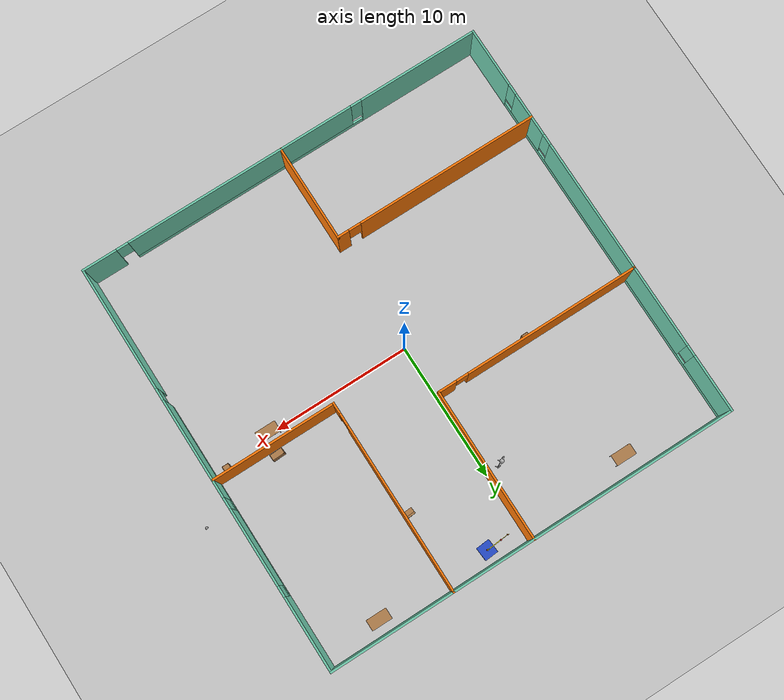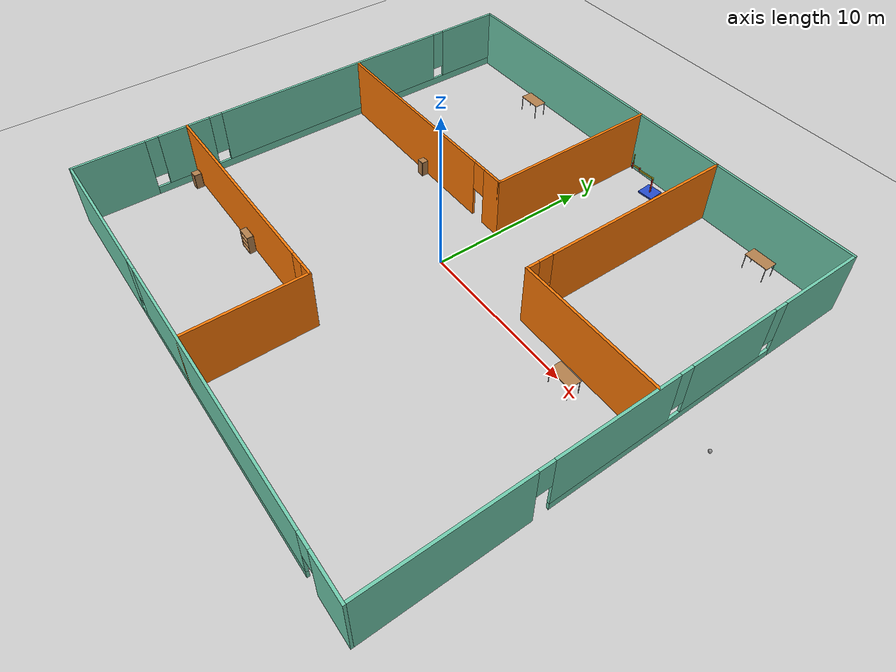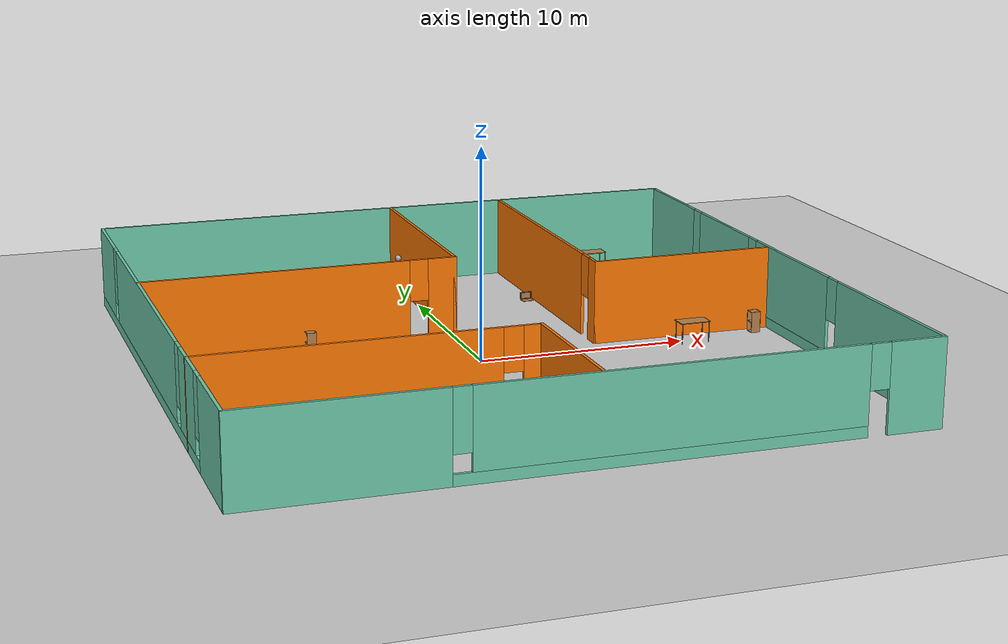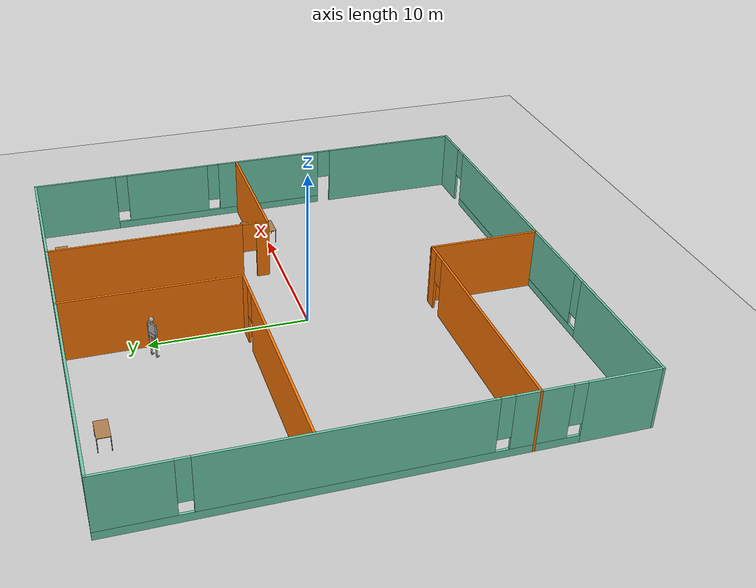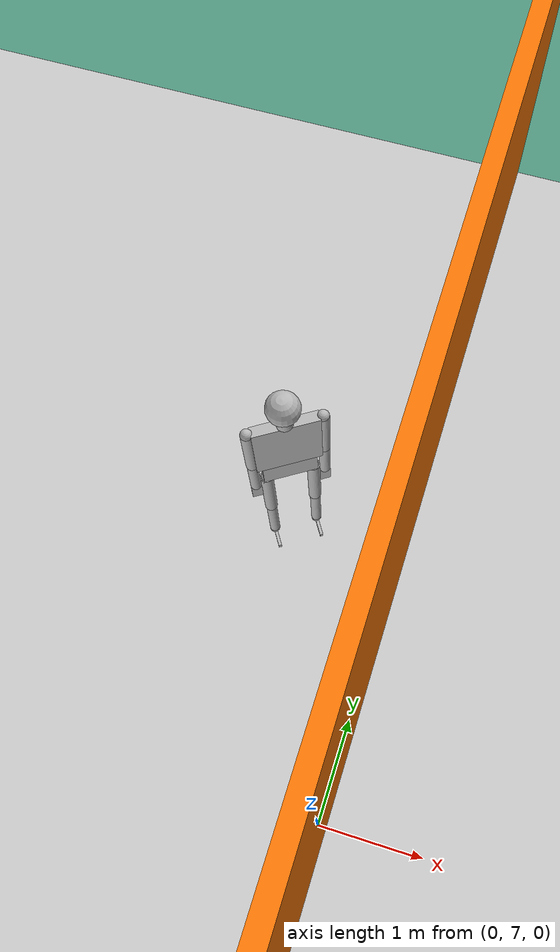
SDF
<sdf version="1.6">
 <world name="default">
  <plugin name="hello" filename="libhello.so"/>
  <light name="sun" type="directional">
   <pose>0 0 10 0 -0 0</pose>
   <diffuse>0.8 0.8 0.8 1</diffuse>
   <specular>0.2 0.2 0.2 1</specular>
   <attenuation>
    <range>1000</range>
    <constant>0.9</constant>
    <linear>0.01</linear>
    <quadratic>0.001</quadratic>
   </attenuation>
   <direction>-0.5 0.1 -0.9</direction>
  </light>
  <model name="ground_plane">
   <static>1</static>
   <link name="link">
    <collision name="collision">
     <geometry><plane><normal>0 0 1</normal><size>100 100</size></plane></geometry>
     <surface>
      <contact><collide_bitmask>65535</collide_bitmask></contact>
      <friction><ode><mu>100</mu><mu2>50</mu2></ode></friction>
     </surface>
    </collision>
    <visual name="visual">
     <cast_shadows>0</cast_shadows>
     <geometry><plane><normal>0 0 1</normal><size>100 100</size></plane></geometry>
     <material>
      <script><uri>file://media/materials/scripts/gazebo.material</uri><name>Gazebo/Grey</name></script>
     </material>
    </visual>
   </link>
  </model>
  <gravity>0 0 -9.8</gravity>
  <magnetic_field>6e-06 2.3e-05 -4.2e-05</magnetic_field>
  <atmosphere type="adiabatic"/>
  <physics name="default_physics" default="0" type="ode">
   <max_step_size>0.001</max_step_size>
   <real_time_factor>1</real_time_factor>
   <real_time_update_rate>1000</real_time_update_rate>
  </physics>
  <scene><ambient>0.4 0.4 0.4 1</ambient><background>0.7 0.7 0.7 1</background><shadows>1</shadows></scene>
  <spherical_coordinates>
   <surface_model>EARTH_WGS84</surface_model>
   <latitude_deg>0</latitude_deg>
   <longitude_deg>0</longitude_deg>
   <elevation>0</elevation>
   <heading_deg>0</heading_deg>
  </spherical_coordinates>
  <model name="mybuilding">
   <link name="Wall_0">
    <pose>0 -15 0 0 -0 0</pose>
    <visual name="Wall_0_Visual_0">
     <pose>-10.633 0 2 0 -0 0</pose>
     <geometry><box><size>8.884 0.15 4</size></box></geometry>
     <material>
      <script><uri>file://media/materials/scripts/gazebo.material</uri><name>Gazebo/Grey</name></script>
      <ambient>0.435294 0.796078 0.67451 1</ambient>
     </material>
     <meta><layer>0</layer></meta>
    </visual>
    <collision name="Wall_0_Collision_0">
     <geometry><box><size>8.884 0.15 4</size></box></geometry>
     <pose>-10.633 0 2 0 -0 0</pose>
    </collision>
    <visual name="Wall_0_Visual_1">
     <pose>13.7885 0 2 0 -0 0</pose>
     <geometry><box><size>2.57292 0.15 4</size></box></geometry>
     <material>
      <script><uri>file://media/materials/scripts/gazebo.material</uri><name>Gazebo/Grey</name></script>
      <ambient>0.435294 0.796078 0.67451 1</ambient>
     </material>
     <meta><layer>0</layer></meta>
    </visual>
    <collision name="Wall_0_Collision_1">
     <geometry><box><size>2.57292 0.15 4</size></box></geometry>
     <pose>13.7885 0 2 0 -0 0</pose>
    </collision>
    <visual name="Wall_0_Visual_2">
     <pose>2.70554 0 0.25 0 -0 0</pose>
     <geometry><box><size>17.7931 0.15 0.5</size></box></geometry>
     <material>
      <script><uri>file://media/materials/scripts/gazebo.material</uri><name>Gazebo/Grey</name></script>
      <ambient>0.435294 0.796078 0.67451 1</ambient>
     </material>
     <meta><layer>0</layer></meta>
    </visual>
    <collision name="Wall_0_Collision_2">
     <geometry><box><size>17.7931 0.15 0.5</size></box></geometry>
     <pose>2.70554 0 0.25 0 -0 0</pose>
    </collision>
    <visual name="Wall_0_Visual_3">
     <pose>3.10554 0 2.25 0 -0 0</pose>
     <geometry><box><size>16.9931 0.15 3.5</size></box></geometry>
     <material>
      <script><uri>file://media/materials/scripts/gazebo.material</uri><name>Gazebo/Grey</name></script>
      <ambient>0.435294 0.796078 0.67451 1</ambient>
     </material>
     <meta><layer>0</layer></meta>
    </visual>
    <collision name="Wall_0_Collision_3">
     <geometry><box><size>16.9931 0.15 3.5</size></box></geometry>
     <pose>3.10554 0 2.25 0 -0 0</pose>
    </collision>
    <visual name="Wall_0_Visual_4">
     <pose>-5.791 0 2.65 0 -0 0</pose>
     <geometry><box><size>0.8 0.15 2.7</size></box></geometry>
     <material>
      <script><uri>file://media/materials/scripts/gazebo.material</uri><name>Gazebo/Grey</name></script>
      <ambient>0.435294 0.796078 0.67451 1</ambient>
     </material>
     <meta><layer>0</layer></meta>
    </visual>
    <collision name="Wall_0_Collision_4">
     <geometry><box><size>0.8 0.15 2.7</size></box></geometry>
     <pose>-5.791 0 2.65 0 -0 0</pose>
    </collision>
    <visual name="Wall_0_Visual_5">
     <pose>12.0521 0 3 0 -0 0</pose>
     <geometry><box><size>0.9 0.15 2</size></box></geometry>
     <material>
      <script><uri>file://media/materials/scripts/gazebo.material</uri><name>Gazebo/Grey</name></script>
      <ambient>0.435294 0.796078 0.67451 1</ambient>
     </material>
     <meta><layer>0</layer></meta>
    </visual>
    <collision name="Wall_0_Collision_5">
     <geometry><box><size>0.9 0.15 2</size></box></geometry>
     <pose>12.0521 0 3 0 -0 0</pose>
    </collision>
   </link>
   <link name="Wall_11">
    <pose>6 8 0 0 0 -1.5708</pose>
    <visual name="Wall_11_Visual_0">
     <pose>-0.873456 0 2 0 -0 0</pose>
     <geometry><box><size>12.4031 0.15 4</size></box></geometry>
     <material>
      <script><uri>file://media/materials/scripts/gazebo.material</uri><name>Gazebo/Grey</name></script>
      <ambient>0.996078 0.47451 0.0196078 1</ambient>
     </material>
     <meta><layer>0</layer></meta>
    </visual>
    <collision name="Wall_11_Collision_0">
     <geometry><box><size>12.4031 0.15 4</size></box></geometry>
     <pose>-0.873456 0 2 0 -0 0</pose>
    </collision>
    <visual name="Wall_11_Visual_1">
     <pose>6.65154 0 2 0 -0 0</pose>
     <geometry><box><size>0.846912 0.15 4</size></box></geometry>
     <material>
      <script><uri>file://media/materials/scripts/gazebo.material</uri><name>Gazebo/Grey</name></script>
      <ambient>0.996078 0.47451 0.0196078 1</ambient>
     </material>
     <meta><layer>0</layer></meta>
    </visual>
    <collision name="Wall_11_Collision_1">
     <geometry><box><size>0.846912 0.15 4</size></box></geometry>
     <pose>6.65154 0 2 0 -0 0</pose>
    </collision>
    <visual name="Wall_11_Visual_2">
     <pose>5.77809 0 3 0 -0 0</pose>
     <geometry><box><size>0.9 0.15 2</size></box></geometry>
     <material>
      <script><uri>file://media/materials/scripts/gazebo.material</uri><name>Gazebo/Grey</name></script>
      <ambient>0.996078 0.47451 0.0196078 1</ambient>
     </material>
     <meta><layer>0</layer></meta>
    </visual>
    <collision name="Wall_11_Collision_2">
     <geometry><box><size>0.9 0.15 2</size></box></geometry>
     <pose>5.77809 0 3 0 -0 0</pose>
    </collision>
   </link>
   <link name="Wall_12">
    <collision name="Wall_12_Collision">
     <geometry><box><size>9.15 0.15 4</size></box></geometry>
     <pose>0 0 2 0 -0 0</pose>
    </collision>
    <visual name="Wall_12_Visual">
     <pose>0 0 2 0 -0 0</pose>
     <geometry><box><size>9.15 0.15 4</size></box></geometry>
     <material>
      <script><uri>file://media/materials/scripts/gazebo.material</uri><name>Gazebo/Grey</name></script>
      <ambient>0.996078 0.47451 0.0196078 1</ambient>
     </material>
     <meta><layer>0</layer></meta>
    </visual>
    <pose>10.5 1 0 0 -0 0</pose>
   </link>
   <link name="Wall_15">
    <pose>-7.5 -8 0 0 -0 0</pose>
    <visual name="Wall_15_Visual_0">
     <pose>-0.899366 0 2 0 -0 0</pose>
     <geometry><box><size>13.3513 0.15 4</size></box></geometry>
     <material>
      <script><uri>file://media/materials/scripts/gazebo.material</uri><name>Gazebo/Grey</name></script>
      <ambient>0.996078 0.47451 0.0196078 1</ambient>
     </material>
     <meta><layer>0</layer></meta>
    </visual>
    <collision name="Wall_15_Collision_0">
     <geometry><box><size>13.3513 0.15 4</size></box></geometry>
     <pose>-0.899366 0 2 0 -0 0</pose>
    </collision>
    <visual name="Wall_15_Visual_1">
     <pose>7.12563 0 2 0 -0 0</pose>
     <geometry><box><size>0.898731 0.15 4</size></box></geometry>
     <material>
      <script><uri>file://media/materials/scripts/gazebo.material</uri><name>Gazebo/Grey</name></script>
      <ambient>0.996078 0.47451 0.0196078 1</ambient>
     </material>
     <meta><layer>0</layer></meta>
    </visual>
    <collision name="Wall_15_Collision_1">
     <geometry><box><size>0.898731 0.15 4</size></box></geometry>
     <pose>7.12563 0 2 0 -0 0</pose>
    </collision>
    <visual name="Wall_15_Visual_2">
     <pose>6.22627 0 3 0 -0 0</pose>
     <geometry><box><size>0.9 0.15 2</size></box></geometry>
     <material>
      <script><uri>file://media/materials/scripts/gazebo.material</uri><name>Gazebo/Grey</name></script>
      <ambient>0.996078 0.47451 0.0196078 1</ambient>
     </material>
     <meta><layer>0</layer></meta>
    </visual>
    <collision name="Wall_15_Collision_2">
     <geometry><box><size>0.9 0.15 2</size></box></geometry>
     <pose>6.22627 0 3 0 -0 0</pose>
    </collision>
   </link>
   <link name="Wall_16">
    <collision name="Wall_16_Collision">
     <geometry><box><size>7.15 0.15 4</size></box></geometry>
     <pose>0 0 2 0 -0 0</pose>
    </collision>
    <visual name="Wall_16_Visual">
     <pose>0 0 2 0 -0 0</pose>
     <geometry><box><size>7.15 0.15 4</size></box></geometry>
     <material>
      <script><uri>file://media/materials/scripts/gazebo.material</uri><name>Gazebo/Grey</name></script>
      <ambient>0.996078 0.47451 0.0196078 1</ambient>
     </material>
     <meta><layer>0</layer></meta>
    </visual>
    <pose>0 -11.5 0 0 0 -1.5708</pose>
   </link>
   <link name="Wall_2">
    <pose>-15 0 0 0 -0 1.5708</pose>
    <visual name="Wall_2_Visual_0">
     <pose>-12.8592 0 2 0 -0 0</pose>
     <geometry><box><size>4.43152 0.15 4</size></box></geometry>
     <material>
      <script><uri>file://media/materials/scripts/gazebo.material</uri><name>Gazebo/Grey</name></script>
      <ambient>0.435294 0.796078 0.67451 1</ambient>
     </material>
     <meta><layer>0</layer></meta>
    </visual>
    <collision name="Wall_2_Collision_0">
     <geometry><box><size>4.43152 0.15 4</size></box></geometry>
     <pose>-12.8592 0 2 0 -0 0</pose>
    </collision>
    <visual name="Wall_2_Visual_1">
     <pose>2.21576 0 0.25 0 -0 0</pose>
     <geometry><box><size>25.7185 0.15 0.5</size></box></geometry>
     <material>
      <script><uri>file://media/materials/scripts/gazebo.material</uri><name>Gazebo/Grey</name></script>
      <ambient>0.435294 0.796078 0.67451 1</ambient>
     </material>
     <meta><layer>0</layer></meta>
    </visual>
    <collision name="Wall_2_Collision_1">
     <geometry><box><size>25.7185 0.15 0.5</size></box></geometry>
     <pose>2.21576 0 0.25 0 -0 0</pose>
    </collision>
    <visual name="Wall_2_Visual_2">
     <pose>-8.20692 0 2.25 0 -0 0</pose>
     <geometry><box><size>3.27311 0.15 3.5</size></box></geometry>
     <material>
      <script><uri>file://media/materials/scripts/gazebo.material</uri><name>Gazebo/Grey</name></script>
      <ambient>0.435294 0.796078 0.67451 1</ambient>
     </material>
     <meta><layer>0</layer></meta>
    </visual>
    <collision name="Wall_2_Collision_2">
     <geometry><box><size>3.27311 0.15 3.5</size></box></geometry>
     <pose>-8.20692 0 2.25 0 -0 0</pose>
    </collision>
    <visual name="Wall_2_Visual_3">
     <pose>2.1359 0 2.25 0 -0 0</pose>
     <geometry><box><size>15.8125 0.15 3.5</size></box></geometry>
     <material>
      <script><uri>file://media/materials/scripts/gazebo.material</uri><name>Gazebo/Grey</name></script>
      <ambient>0.435294 0.796078 0.67451 1</ambient>
     </material>
     <meta><layer>0</layer></meta>
    </visual>
    <collision name="Wall_2_Collision_3">
     <geometry><box><size>15.8125 0.15 3.5</size></box></geometry>
     <pose>2.1359 0 2.25 0 -0 0</pose>
    </collision>
    <visual name="Wall_2_Visual_4">
     <pose>12.9586 0 2.25 0 -0 0</pose>
     <geometry><box><size>4.23284 0.15 3.5</size></box></geometry>
     <material>
      <script><uri>file://media/materials/scripts/gazebo.material</uri><name>Gazebo/Grey</name></script>
      <ambient>0.435294 0.796078 0.67451 1</ambient>
     </material>
     <meta><layer>0</layer></meta>
    </visual>
    <collision name="Wall_2_Collision_4">
     <geometry><box><size>4.23284 0.15 3.5</size></box></geometry>
     <pose>12.9586 0 2.25 0 -0 0</pose>
    </collision>
    <visual name="Wall_2_Visual_5">
     <pose>-10.2435 0 2.65 0 -0 0</pose>
     <geometry><box><size>0.8 0.15 2.7</size></box></geometry>
     <material>
      <script><uri>file://media/materials/scripts/gazebo.material</uri><name>Gazebo/Grey</name></script>
      <ambient>0.435294 0.796078 0.67451 1</ambient>
     </material>
     <meta><layer>0</layer></meta>
    </visual>
    <collision name="Wall_2_Collision_5">
     <geometry><box><size>0.8 0.15 2.7</size></box></geometry>
     <pose>-10.2435 0 2.65 0 -0 0</pose>
    </collision>
    <visual name="Wall_2_Visual_6">
     <pose>-6.17037 0 2.65 0 -0 0</pose>
     <geometry><box><size>0.8 0.15 2.7</size></box></geometry>
     <material>
      <script><uri>file://media/materials/scripts/gazebo.material</uri><name>Gazebo/Grey</name></script>
      <ambient>0.435294 0.796078 0.67451 1</ambient>
     </material>
     <meta><layer>0</layer></meta>
    </visual>
    <collision name="Wall_2_Collision_6">
     <geometry><box><size>0.8 0.15 2.7</size></box></geometry>
     <pose>-6.17037 0 2.65 0 -0 0</pose>
    </collision>
    <visual name="Wall_2_Visual_7">
     <pose>10.4422 0 2.65 0 -0 0</pose>
     <geometry><box><size>0.8 0.15 2.7</size></box></geometry>
     <material>
      <script><uri>file://media/materials/scripts/gazebo.material</uri><name>Gazebo/Grey</name></script>
      <ambient>0.435294 0.796078 0.67451 1</ambient>
     </material>
     <meta><layer>0</layer></meta>
    </visual>
    <collision name="Wall_2_Collision_7">
     <geometry><box><size>0.8 0.15 2.7</size></box></geometry>
     <pose>10.4422 0 2.65 0 -0 0</pose>
    </collision>
   </link>
   <link name="Wall_4">
    <collision name="Wall_4_Collision">
     <geometry><box><size>30.15 0.15 4</size></box></geometry>
     <pose>0 0 2 0 -0 0</pose>
    </collision>
    <visual name="Wall_4_Visual">
     <pose>0 0 2 0 -0 0</pose>
     <geometry><box><size>30.15 0.15 4</size></box></geometry>
     <material>
      <script><uri>file://media/materials/scripts/gazebo.material</uri><name>Gazebo/Grey</name></script>
      <ambient>0.435294 0.796078 0.67451 1</ambient>
     </material>
     <meta><layer>0</layer></meta>
    </visual>
    <pose>0 15 0 0 -0 0</pose>
   </link>
   <link name="Wall_6">
    <pose>15 0 0 0 0 -1.5708</pose>
    <visual name="Wall_6_Visual_0">
     <pose>-12.3389 0 2 0 -0 0</pose>
     <geometry><box><size>5.47227 0.15 4</size></box></geometry>
     <material>
      <script><uri>file://media/materials/scripts/gazebo.material</uri><name>Gazebo/Grey</name></script>
      <ambient>0.435294 0.796078 0.67451 1</ambient>
     </material>
     <meta><layer>0</layer></meta>
    </visual>
    <collision name="Wall_6_Collision_0">
     <geometry><box><size>5.47227 0.15 4</size></box></geometry>
     <pose>-12.3389 0 2 0 -0 0</pose>
    </collision>
    <visual name="Wall_6_Visual_1">
     <pose>10.4919 0 2 0 -0 0</pose>
     <geometry><box><size>9.16611 0.15 4</size></box></geometry>
     <material>
      <script><uri>file://media/materials/scripts/gazebo.material</uri><name>Gazebo/Grey</name></script>
      <ambient>0.435294 0.796078 0.67451 1</ambient>
     </material>
     <meta><layer>0</layer></meta>
    </visual>
    <collision name="Wall_6_Collision_1">
     <geometry><box><size>9.16611 0.15 4</size></box></geometry>
     <pose>10.4919 0 2 0 -0 0</pose>
    </collision>
    <visual name="Wall_6_Visual_2">
     <pose>-2.29692 0 0.25 0 -0 0</pose>
     <geometry><box><size>14.6116 0.15 0.5</size></box></geometry>
     <material>
      <script><uri>file://media/materials/scripts/gazebo.material</uri><name>Gazebo/Grey</name></script>
      <ambient>0.435294 0.796078 0.67451 1</ambient>
     </material>
     <meta><layer>0</layer></meta>
    </visual>
    <collision name="Wall_6_Collision_2">
     <geometry><box><size>14.6116 0.15 0.5</size></box></geometry>
     <pose>-2.29692 0 0.25 0 -0 0</pose>
    </collision>
    <visual name="Wall_6_Visual_3">
     <pose>-5.96326 0 2.25 0 -0 0</pose>
     <geometry><box><size>5.67893 0.15 3.5</size></box></geometry>
     <material>
      <script><uri>file://media/materials/scripts/gazebo.material</uri><name>Gazebo/Grey</name></script>
      <ambient>0.435294 0.796078 0.67451 1</ambient>
     </material>
     <meta><layer>0</layer></meta>
    </visual>
    <collision name="Wall_6_Collision_3">
     <geometry><box><size>5.67893 0.15 3.5</size></box></geometry>
     <pose>-5.96326 0 2.25 0 -0 0</pose>
    </collision>
    <visual name="Wall_6_Visual_4">
     <pose>1.34255 0 2.25 0 -0 0</pose>
     <geometry><box><size>7.3327 0.15 3.5</size></box></geometry>
     <material>
      <script><uri>file://media/materials/scripts/gazebo.material</uri><name>Gazebo/Grey</name></script>
      <ambient>0.435294 0.796078 0.67451 1</ambient>
     </material>
     <meta><layer>0</layer></meta>
    </visual>
    <collision name="Wall_6_Collision_4">
     <geometry><box><size>7.3327 0.15 3.5</size></box></geometry>
     <pose>1.34255 0 2.25 0 -0 0</pose>
    </collision>
    <visual name="Wall_6_Visual_5">
     <pose>-9.20273 0 2.65 0 -0 0</pose>
     <geometry><box><size>0.8 0.15 2.7</size></box></geometry>
     <material>
      <script><uri>file://media/materials/scripts/gazebo.material</uri><name>Gazebo/Grey</name></script>
      <ambient>0.435294 0.796078 0.67451 1</ambient>
     </material>
     <meta><layer>0</layer></meta>
    </visual>
    <collision name="Wall_6_Collision_5">
     <geometry><box><size>0.8 0.15 2.7</size></box></geometry>
     <pose>-9.20273 0 2.65 0 -0 0</pose>
    </collision>
    <visual name="Wall_6_Visual_6">
     <pose>-2.7238 0 2.65 0 -0 0</pose>
     <geometry><box><size>0.8 0.15 2.7</size></box></geometry>
     <material>
      <script><uri>file://media/materials/scripts/gazebo.material</uri><name>Gazebo/Grey</name></script>
      <ambient>0.435294 0.796078 0.67451 1</ambient>
     </material>
     <meta><layer>0</layer></meta>
    </visual>
    <collision name="Wall_6_Collision_6">
     <geometry><box><size>0.8 0.15 2.7</size></box></geometry>
     <pose>-2.7238 0 2.65 0 -0 0</pose>
    </collision>
    <visual name="Wall_6_Visual_7">
     <pose>5.45889 0 3 0 -0 0</pose>
     <geometry><box><size>0.9 0.15 2</size></box></geometry>
     <material>
      <script><uri>file://media/materials/scripts/gazebo.material</uri><name>Gazebo/Grey</name></script>
      <ambient>0.435294 0.796078 0.67451 1</ambient>
     </material>
     <meta><layer>0</layer></meta>
    </visual>
    <collision name="Wall_6_Collision_7">
     <geometry><box><size>0.9 0.15 2</size></box></geometry>
     <pose>5.45889 0 3 0 -0 0</pose>
    </collision>
   </link>
   <link name="Wall_8">
    <pose>-7.5 4 0 0 -0 0</pose>
    <visual name="Wall_8_Visual_0">
     <pose>-1.15244 0 2 0 -0 0</pose>
     <geometry><box><size>12.8451 0.15 4</size></box></geometry>
     <material>
      <script><uri>file://media/materials/scripts/gazebo.material</uri><name>Gazebo/Grey</name></script>
      <ambient>0.996078 0.47451 0.0196078 1</ambient>
     </material>
     <meta><layer>0</layer></meta>
    </visual>
    <collision name="Wall_8_Collision_0">
     <geometry><box><size>12.8451 0.15 4</size></box></geometry>
     <pose>-1.15244 0 2 0 -0 0</pose>
    </collision>
    <visual name="Wall_8_Visual_1">
     <pose>6.87256 0 2 0 -0 0</pose>
     <geometry><box><size>1.40488 0.15 4</size></box></geometry>
     <material>
      <script><uri>file://media/materials/scripts/gazebo.material</uri><name>Gazebo/Grey</name></script>
      <ambient>0.996078 0.47451 0.0196078 1</ambient>
     </material>
     <meta><layer>0</layer></meta>
    </visual>
    <collision name="Wall_8_Collision_1">
     <geometry><box><size>1.40488 0.15 4</size></box></geometry>
     <pose>6.87256 0 2 0 -0 0</pose>
    </collision>
    <visual name="Wall_8_Visual_2">
     <pose>5.72012 0 3 0 -0 0</pose>
     <geometry><box><size>0.9 0.15 2</size></box></geometry>
     <material>
      <script><uri>file://media/materials/scripts/gazebo.material</uri><name>Gazebo/Grey</name></script>
      <ambient>0.996078 0.47451 0.0196078 1</ambient>
     </material>
     <meta><layer>0</layer></meta>
    </visual>
    <collision name="Wall_8_Collision_2">
     <geometry><box><size>0.9 0.15 2</size></box></geometry>
     <pose>5.72012 0 3 0 -0 0</pose>
    </collision>
   </link>
   <link name="Wall_9">
    <collision name="Wall_9_Collision">
     <geometry><box><size>11.15 0.15 4</size></box></geometry>
     <pose>0 0 2 0 -0 0</pose>
    </collision>
    <visual name="Wall_9_Visual">
     <pose>0 0 2 0 -0 0</pose>
     <geometry><box><size>11.15 0.15 4</size></box></geometry>
     <material>
      <script><uri>file://media/materials/scripts/gazebo.material</uri><name>Gazebo/Grey</name></script>
      <ambient>0.996078 0.47451 0.0196078 1</ambient>
     </material>
     <meta><layer>0</layer></meta>
    </visual>
    <pose>0 9.5 0 0 -0 1.5708</pose>
   </link>
   <static>1</static>
  </model>
  <model name="table">
   <static>1</static>
   <link name="link">
    <collision name="surface">
     <pose>0 0 1 0 -0 0</pose>
     <geometry><box><size>1.5 0.8 0.03</size></box></geometry>
     <surface><friction><ode><mu>0.6</mu><mu2>0.6</mu2></ode></friction></surface>
    </collision>
    <visual name="visual1">
     <pose>0 0 1 0 -0 0</pose>
     <geometry><box><size>1.5 0.8 0.03</size></box></geometry>
     <material>
      <script><uri>file://media/materials/scripts/gazebo.material</uri><name>Gazebo/Wood</name></script>
     </material>
    </visual>
    <collision name="front_left_leg">
     <pose>0.68 0.38 0.5 0 -0 0</pose>
     <geometry><cylinder><radius>0.02</radius><length>1</length></cylinder></geometry>
    </collision>
    <visual name="front_left_leg">
     <pose>0.68 0.38 0.5 0 -0 0</pose>
     <geometry><cylinder><radius>0.02</radius><length>1</length></cylinder></geometry>
     <material>
      <script><uri>file://media/materials/scripts/gazebo.material</uri><name>Gazebo/Grey</name></script>
     </material>
    </visual>
    <collision name="front_right_leg">
     <pose>0.68 -0.38 0.5 0 -0 0</pose>
     <geometry><cylinder><radius>0.02</radius><length>1</length></cylinder></geometry>
    </collision>
    <visual name="front_right_leg">
     <pose>0.68 -0.38 0.5 0 -0 0</pose>
     <geometry><cylinder><radius>0.02</radius><length>1</length></cylinder></geometry>
     <material>
      <script><uri>file://media/materials/scripts/gazebo.material</uri><name>Gazebo/Grey</name></script>
     </material>
    </visual>
    <collision name="back_right_leg">
     <pose>-0.68 -0.38 0.5 0 -0 0</pose>
     <geometry><cylinder><radius>0.02</radius><length>1</length></cylinder></geometry>
    </collision>
    <visual name="back_right_leg">
     <pose>-0.68 -0.38 0.5 0 -0 0</pose>
     <geometry><cylinder><radius>0.02</radius><length>1</length></cylinder></geometry>
     <material>
      <script><uri>file://media/materials/scripts/gazebo.material</uri><name>Gazebo/Grey</name></script>
     </material>
    </visual>
    <collision name="back_left_leg">
     <pose>-0.68 0.38 0.5 0 -0 0</pose>
     <geometry><cylinder><radius>0.02</radius><length>1</length></cylinder></geometry>
    </collision>
    <visual name="back_left_leg">
     <pose>-0.68 0.38 0.5 0 -0 0</pose>
     <geometry><cylinder><radius>0.02</radius><length>1</length></cylinder></geometry>
     <material>
      <script><uri>file://media/materials/scripts/gazebo.material</uri><name>Gazebo/Grey</name></script>
     </material>
    </visual>
   </link>
   <pose>10.5355 -0.123051 0 0 -0 0</pose>
  </model>
  <model name="table_0">
   <static>1</static>
   <link name="link">
    <collision name="surface">
     <pose>0 0 1 0 -0 0</pose>
     <geometry><box><size>1.5 0.8 0.03</size></box></geometry>
     <surface><friction><ode><mu>0.6</mu><mu2>0.6</mu2></ode></friction></surface>
    </collision>
    <visual name="visual1">
     <pose>0 0 1 0 -0 0</pose>
     <geometry><box><size>1.5 0.8 0.03</size></box></geometry>
     <material>
      <script><uri>file://media/materials/scripts/gazebo.material</uri><name>Gazebo/Wood</name></script>
     </material>
    </visual>
    <collision name="front_left_leg">
     <pose>0.68 0.38 0.5 0 -0 0</pose>
     <geometry><cylinder><radius>0.02</radius><length>1</length></cylinder></geometry>
    </collision>
    <visual name="front_left_leg">
     <pose>0.68 0.38 0.5 0 -0 0</pose>
     <geometry><cylinder><radius>0.02</radius><length>1</length></cylinder></geometry>
     <material>
      <script><uri>file://media/materials/scripts/gazebo.material</uri><name>Gazebo/Grey</name></script>
     </material>
    </visual>
    <collision name="front_right_leg">
     <pose>0.68 -0.38 0.5 0 -0 0</pose>
     <geometry><cylinder><radius>0.02</radius><length>1</length></cylinder></geometry>
    </collision>
    <visual name="front_right_leg">
     <pose>0.68 -0.38 0.5 0 -0 0</pose>
     <geometry><cylinder><radius>0.02</radius><length>1</length></cylinder></geometry>
     <material>
      <script><uri>file://media/materials/scripts/gazebo.material</uri><name>Gazebo/Grey</name></script>
     </material>
    </visual>
    <collision name="back_right_leg">
     <pose>-0.68 -0.38 0.5 0 -0 0</pose>
     <geometry><cylinder><radius>0.02</radius><length>1</length></cylinder></geometry>
    </collision>
    <visual name="back_right_leg">
     <pose>-0.68 -0.38 0.5 0 -0 0</pose>
     <geometry><cylinder><radius>0.02</radius><length>1</length></cylinder></geometry>
     <material>
      <script><uri>file://media/materials/scripts/gazebo.material</uri><name>Gazebo/Grey</name></script>
     </material>
    </visual>
    <collision name="back_left_leg">
     <pose>-0.68 0.38 0.5 0 -0 0</pose>
     <geometry><cylinder><radius>0.02</radius><length>1</length></cylinder></geometry>
    </collision>
    <visual name="back_left_leg">
     <pose>-0.68 0.38 0.5 0 -0 0</pose>
     <geometry><cylinder><radius>0.02</radius><length>1</length></cylinder></geometry>
     <material>
      <script><uri>file://media/materials/scripts/gazebo.material</uri><name>Gazebo/Grey</name></script>
     </material>
    </visual>
   </link>
   <pose>10.8819 13.9467 0 0 -0 0</pose>
  </model>
  <model name="table_1">
   <static>1</static>
   <link name="link">
    <collision name="surface">
     <pose>0 0 1 0 -0 0</pose>
     <geometry><box><size>1.5 0.8 0.03</size></box></geometry>
     <surface><friction><ode><mu>0.6</mu><mu2>0.6</mu2></ode></friction></surface>
    </collision>
    <visual name="visual1">
     <pose>0 0 1 0 -0 0</pose>
     <geometry><box><size>1.5 0.8 0.03</size></box></geometry>
     <material>
      <script><uri>file://media/materials/scripts/gazebo.material</uri><name>Gazebo/Wood</name></script>
     </material>
    </visual>
    <collision name="front_left_leg">
     <pose>0.68 0.38 0.5 0 -0 0</pose>
     <geometry><cylinder><radius>0.02</radius><length>1</length></cylinder></geometry>
    </collision>
    <visual name="front_left_leg">
     <pose>0.68 0.38 0.5 0 -0 0</pose>
     <geometry><cylinder><radius>0.02</radius><length>1</length></cylinder></geometry>
     <material>
      <script><uri>file://media/materials/scripts/gazebo.material</uri><name>Gazebo/Grey</name></script>
     </material>
    </visual>
    <collision name="front_right_leg">
     <pose>0.68 -0.38 0.5 0 -0 0</pose>
     <geometry><cylinder><radius>0.02</radius><length>1</length></cylinder></geometry>
    </collision>
    <visual name="front_right_leg">
     <pose>0.68 -0.38 0.5 0 -0 0</pose>
     <geometry><cylinder><radius>0.02</radius><length>1</length></cylinder></geometry>
     <material>
      <script><uri>file://media/materials/scripts/gazebo.material</uri><name>Gazebo/Grey</name></script>
     </material>
    </visual>
    <collision name="back_right_leg">
     <pose>-0.68 -0.38 0.5 0 -0 0</pose>
     <geometry><cylinder><radius>0.02</radius><length>1</length></cylinder></geometry>
    </collision>
    <visual name="back_right_leg">
     <pose>-0.68 -0.38 0.5 0 -0 0</pose>
     <geometry><cylinder><radius>0.02</radius><length>1</length></cylinder></geometry>
     <material>
      <script><uri>file://media/materials/scripts/gazebo.material</uri><name>Gazebo/Grey</name></script>
     </material>
    </visual>
    <collision name="back_left_leg">
     <pose>-0.68 0.38 0.5 0 -0 0</pose>
     <geometry><cylinder><radius>0.02</radius><length>1</length></cylinder></geometry>
    </collision>
    <visual name="back_left_leg">
     <pose>-0.68 0.38 0.5 0 -0 0</pose>
     <geometry><cylinder><radius>0.02</radius><length>1</length></cylinder></geometry>
     <material>
      <script><uri>file://media/materials/scripts/gazebo.material</uri><name>Gazebo/Grey</name></script>
     </material>
    </visual>
   </link>
   <pose>-8.17973 13.6528 0 0 -0 0</pose>
  </model>
  <model name="my_ball">
   <link name="link_0">
    <inertial>
     <mass>1</mass>
     <inertia><ixx>0.1</ixx><ixy>0</ixy><ixz>0</ixz><iyy>0.1</iyy><iyz>0</iyz><izz>0.1</izz></inertia>
    </inertial>
    <visual name="visual">
     <geometry><sphere><radius>0.1</radius></sphere></geometry>
     <material>
      <lighting>1</lighting>
      <script><uri>file://media/materials/scripts/gazebo.material</uri><name>Gazebo/Grey</name></script>
      <shader type="pixel"><normal_map>__default__</normal_map></shader>
      <ambient>1 1 1 1</ambient>
      <diffuse>1 1 1 1</diffuse>
      <specular>1 1 1 1</specular>
      <emissive>1 1 1 1</emissive>
     </material>
    </visual>
    <collision name="collision">
     <geometry><sphere><radius>0.1</radius></sphere></geometry>
     <surface>
      <friction>
       <ode><mu>1</mu><mu2>1</mu2><fdir1>0 0 0</fdir1><slip1>0</slip1><slip2>0</slip2></ode>
       <torsional>
        <coefficient>1</coefficient>
        <patch_radius>0</patch_radius>
        <surface_radius>0</surface_radius>
        <use_patch_radius>1</use_patch_radius>
        <ode><slip>0</slip></ode>
       </torsional>
      </friction>
      <bounce><restitution_coefficient>0</restitution_coefficient><threshold>1e+06</threshold></bounce>
      <contact>
       <collide_without_contact>0</collide_without_contact>
       <collide_without_contact_bitmask>1</collide_without_contact_bitmask>
       <collide_bitmask>1</collide_bitmask>
       <ode>
        <soft_cfm>0</soft_cfm>
        <soft_erp>0.2</soft_erp>
        <kp>1e+13</kp>
        <kd>1</kd>
        <max_vel>0.01</max_vel>
        <min_depth>0</min_depth>
       </ode>
       <bullet>
        <split_impulse>1</split_impulse>
        <split_impulse_penetration_threshold>-0.01</split_impulse_penetration_threshold>
        <soft_cfm>0</soft_cfm>
        <soft_erp>0.2</soft_erp>
        <kp>1e+13</kp>
        <kd>1</kd>
       </bullet>
      </contact>
     </surface>
    </collision>
   </link>
   <static>0</static>
   <pose>17.2325 2.94652 0.1 0 -0 0</pose>
  </model>
  <model name="cabinet">
   <static>1</static>
   <link name="cabinet_bottom_plate">
    <inertial>
     <pose>0 0 -1 0 -0 0</pose>
     <inertia><ixx>2.05</ixx><ixy>0</ixy><ixz>0</ixz><iyy>2.05</iyy><iyz>0</iyz><izz>2.05</izz></inertia>
     <mass>25</mass>
    </inertial>
    <collision name="cabinet_bottom_plate_geom">
     <pose>0 0 0.01 0 -0 0</pose>
     <geometry><box><size>0.45 0.45 0.02</size></box></geometry>
    </collision>
    <visual name="cabinet_bottom_plate_geom_visual">
     <pose>0 0 0.01 0 -0 0</pose>
     <geometry><box><size>0.45 0.45 0.02</size></box></geometry>
     <material>
      <script><uri>file://media/materials/scripts/gazebo.material</uri><name>Gazebo/Wood</name></script>
     </material>
    </visual>
    <collision name="cabinet_bottom_plate_geom_cabinet_back_plate">
     <pose>0.235 0 0.51 0 -0 0</pose>
     <geometry><box><size>0.02 0.45 1.02</size></box></geometry>
    </collision>
    <visual name="cabinet_bottom_plate_geom_cabinet_back_plate_visual">
     <pose>0.235 0 0.51 0 -0 0</pose>
     <geometry><box><size>0.02 0.45 1.02</size></box></geometry>
     <material>
      <script><uri>file://media/materials/scripts/gazebo.material</uri><name>Gazebo/Wood</name></script>
     </material>
    </visual>
    <collision name="cabinet_bottom_plate_geom_cabinet_left_plate">
     <pose>0 0.235 0.51 0 -0 0</pose>
     <geometry><box><size>0.45 0.02 1.02</size></box></geometry>
    </collision>
    <visual name="cabinet_bottom_plate_geom_cabinet_left_plate_visual">
     <pose>0 0.235 0.51 0 -0 0</pose>
     <geometry><box><size>0.45 0.02 1.02</size></box></geometry>
     <material>
      <script><uri>file://media/materials/scripts/gazebo.material</uri><name>Gazebo/Wood</name></script>
     </material>
    </visual>
    <collision name="cabinet_bottom_plate_geom_cabinet_middle_plate">
     <pose>0 0 0.51 0 -0 0</pose>
     <geometry><box><size>0.45 0.45 0.02</size></box></geometry>
    </collision>
    <visual name="cabinet_bottom_plate_geom_cabinet_middle_plate_visual">
     <pose>0 0 0.51 0 -0 0</pose>
     <geometry><box><size>0.45 0.45 0.02</size></box></geometry>
     <material>
      <script><uri>file://media/materials/scripts/gazebo.material</uri><name>Gazebo/Wood</name></script>
     </material>
    </visual>
    <collision name="cabinet_bottom_plate_geom_cabinet_right_plate">
     <pose>0 -0.235 0.51 0 -0 0</pose>
     <geometry><box><size>0.45 0.02 1.02</size></box></geometry>
    </collision>
    <visual name="cabinet_bottom_plate_geom_cabinet_right_plate_visual">
     <pose>0 -0.235 0.51 0 -0 0</pose>
     <geometry><box><size>0.45 0.02 1.02</size></box></geometry>
     <material>
      <script><uri>file://media/materials/scripts/gazebo.material</uri><name>Gazebo/Wood</name></script>
     </material>
    </visual>
    <collision name="cabinet_bottom_plate_geom_cabinet_top_plate">
     <pose>0 0 1.01 0 -0 0</pose>
     <geometry><box><size>0.45 0.45 0.02</size></box></geometry>
    </collision>
    <visual name="cabinet_bottom_plate_geom_cabinet_top_plate_visual">
     <pose>0 0 1.01 0 -0 0</pose>
     <geometry><box><size>0.45 0.45 0.02</size></box></geometry>
     <material>
      <script><uri>file://media/materials/scripts/gazebo.material</uri><name>Gazebo/Wood</name></script>
     </material>
    </visual>
   </link>
   <pose>-7.14243 3.73822 0 0 -0 0</pose>
  </model>
  <model name="cabinet_0">
   <static>1</static>
   <link name="cabinet_bottom_plate">
    <inertial>
     <pose>0 0 -1 0 -0 0</pose>
     <inertia><ixx>2.05</ixx><ixy>0</ixy><ixz>0</ixz><iyy>2.05</iyy><iyz>0</iyz><izz>2.05</izz></inertia>
     <mass>25</mass>
    </inertial>
    <collision name="cabinet_bottom_plate_geom">
     <pose>0 0 0.01 0 -0 0</pose>
     <geometry><box><size>0.45 0.45 0.02</size></box></geometry>
    </collision>
    <visual name="cabinet_bottom_plate_geom_visual">
     <pose>0 0 0.01 0 -0 0</pose>
     <geometry><box><size>0.45 0.45 0.02</size></box></geometry>
     <material>
      <script><uri>file://media/materials/scripts/gazebo.material</uri><name>Gazebo/Wood</name></script>
     </material>
    </visual>
    <collision name="cabinet_bottom_plate_geom_cabinet_back_plate">
     <pose>0.235 0 0.51 0 -0 0</pose>
     <geometry><box><size>0.02 0.45 1.02</size></box></geometry>
    </collision>
    <visual name="cabinet_bottom_plate_geom_cabinet_back_plate_visual">
     <pose>0.235 0 0.51 0 -0 0</pose>
     <geometry><box><size>0.02 0.45 1.02</size></box></geometry>
     <material>
      <script><uri>file://media/materials/scripts/gazebo.material</uri><name>Gazebo/Wood</name></script>
     </material>
    </visual>
    <collision name="cabinet_bottom_plate_geom_cabinet_left_plate">
     <pose>0 0.235 0.51 0 -0 0</pose>
     <geometry><box><size>0.45 0.02 1.02</size></box></geometry>
    </collision>
    <visual name="cabinet_bottom_plate_geom_cabinet_left_plate_visual">
     <pose>0 0.235 0.51 0 -0 0</pose>
     <geometry><box><size>0.45 0.02 1.02</size></box></geometry>
     <material>
      <script><uri>file://media/materials/scripts/gazebo.material</uri><name>Gazebo/Wood</name></script>
     </material>
    </visual>
    <collision name="cabinet_bottom_plate_geom_cabinet_middle_plate">
     <pose>0 0 0.51 0 -0 0</pose>
     <geometry><box><size>0.45 0.45 0.02</size></box></geometry>
    </collision>
    <visual name="cabinet_bottom_plate_geom_cabinet_middle_plate_visual">
     <pose>0 0 0.51 0 -0 0</pose>
     <geometry><box><size>0.45 0.45 0.02</size></box></geometry>
     <material>
      <script><uri>file://media/materials/scripts/gazebo.material</uri><name>Gazebo/Wood</name></script>
     </material>
    </visual>
    <collision name="cabinet_bottom_plate_geom_cabinet_right_plate">
     <pose>0 -0.235 0.51 0 -0 0</pose>
     <geometry><box><size>0.45 0.02 1.02</size></box></geometry>
    </collision>
    <visual name="cabinet_bottom_plate_geom_cabinet_right_plate_visual">
     <pose>0 -0.235 0.51 0 -0 0</pose>
     <geometry><box><size>0.45 0.02 1.02</size></box></geometry>
     <material>
      <script><uri>file://media/materials/scripts/gazebo.material</uri><name>Gazebo/Wood</name></script>
     </material>
    </visual>
    <collision name="cabinet_bottom_plate_geom_cabinet_top_plate">
     <pose>0 0 1.01 0 -0 0</pose>
     <geometry><box><size>0.45 0.45 0.02</size></box></geometry>
    </collision>
    <visual name="cabinet_bottom_plate_geom_cabinet_top_plate_visual">
     <pose>0 0 1.01 0 -0 0</pose>
     <geometry><box><size>0.45 0.45 0.02</size></box></geometry>
     <material>
      <script><uri>file://media/materials/scripts/gazebo.material</uri><name>Gazebo/Wood</name></script>
     </material>
    </visual>
   </link>
   <pose>14.0256 0.459077 0 0 -0 0</pose>
  </model>
  <model name="cabinet_1">
   <static>1</static>
   <link name="cabinet_bottom_plate">
    <inertial>
     <pose>0 0 -1 0 -0 0</pose>
     <inertia><ixx>2.05</ixx><ixy>0</ixy><ixz>0</ixz><iyy>2.05</iyy><iyz>0</iyz><izz>2.05</izz></inertia>
     <mass>25</mass>
    </inertial>
    <collision name="cabinet_bottom_plate_geom">
     <pose>0 0 0.01 0 -0 0</pose>
     <geometry><box><size>0.45 0.45 0.02</size></box></geometry>
    </collision>
    <visual name="cabinet_bottom_plate_geom_visual">
     <pose>0 0 0.01 0 -0 0</pose>
     <geometry><box><size>0.45 0.45 0.02</size></box></geometry>
     <material>
      <script><uri>file://media/materials/scripts/gazebo.material</uri><name>Gazebo/Wood</name></script>
     </material>
    </visual>
    <collision name="cabinet_bottom_plate_geom_cabinet_back_plate">
     <pose>0.235 0 0.51 0 -0 0</pose>
     <geometry><box><size>0.02 0.45 1.02</size></box></geometry>
    </collision>
    <visual name="cabinet_bottom_plate_geom_cabinet_back_plate_visual">
     <pose>0.235 0 0.51 0 -0 0</pose>
     <geometry><box><size>0.02 0.45 1.02</size></box></geometry>
     <material>
      <script><uri>file://media/materials/scripts/gazebo.material</uri><name>Gazebo/Wood</name></script>
     </material>
    </visual>
    <collision name="cabinet_bottom_plate_geom_cabinet_left_plate">
     <pose>0 0.235 0.51 0 -0 0</pose>
     <geometry><box><size>0.45 0.02 1.02</size></box></geometry>
    </collision>
    <visual name="cabinet_bottom_plate_geom_cabinet_left_plate_visual">
     <pose>0 0.235 0.51 0 -0 0</pose>
     <geometry><box><size>0.45 0.02 1.02</size></box></geometry>
     <material>
      <script><uri>file://media/materials/scripts/gazebo.material</uri><name>Gazebo/Wood</name></script>
     </material>
    </visual>
    <collision name="cabinet_bottom_plate_geom_cabinet_middle_plate">
     <pose>0 0 0.51 0 -0 0</pose>
     <geometry><box><size>0.45 0.45 0.02</size></box></geometry>
    </collision>
    <visual name="cabinet_bottom_plate_geom_cabinet_middle_plate_visual">
     <pose>0 0 0.51 0 -0 0</pose>
     <geometry><box><size>0.45 0.45 0.02</size></box></geometry>
     <material>
      <script><uri>file://media/materials/scripts/gazebo.material</uri><name>Gazebo/Wood</name></script>
     </material>
    </visual>
    <collision name="cabinet_bottom_plate_geom_cabinet_right_plate">
     <pose>0 -0.235 0.51 0 -0 0</pose>
     <geometry><box><size>0.45 0.02 1.02</size></box></geometry>
    </collision>
    <visual name="cabinet_bottom_plate_geom_cabinet_right_plate_visual">
     <pose>0 -0.235 0.51 0 -0 0</pose>
     <geometry><box><size>0.45 0.02 1.02</size></box></geometry>
     <material>
      <script><uri>file://media/materials/scripts/gazebo.material</uri><name>Gazebo/Wood</name></script>
     </material>
    </visual>
    <collision name="cabinet_bottom_plate_geom_cabinet_top_plate">
     <pose>0 0 1.01 0 -0 0</pose>
     <geometry><box><size>0.45 0.45 0.02</size></box></geometry>
    </collision>
    <visual name="cabinet_bottom_plate_geom_cabinet_top_plate_visual">
     <pose>0 0 1.01 0 -0 0</pose>
     <geometry><box><size>0.45 0.45 0.02</size></box></geometry>
     <material>
      <script><uri>file://media/materials/scripts/gazebo.material</uri><name>Gazebo/Wood</name></script>
     </material>
    </visual>
   </link>
   <pose>-14.2571 -8.37392 0 0 -0 0</pose>
  </model>
  <model name="bookshelf">
   <static>1</static>
   <link name="link">
    <inertial><mass>1</mass></inertial>
    <collision name="back">
     <pose>0 0.005 0.6 0 -0 0</pose>
     <geometry><box><size>0.9 0.01 1.2</size></box></geometry>
    </collision>
    <visual name="visual1">
     <pose>0 0.005 0.6 0 -0 0</pose>
     <geometry><box><size>0.9 0.01 1.2</size></box></geometry>
     <material>
      <script><uri>file://media/materials/scripts/gazebo.material</uri><name>Gazebo/Wood</name></script>
     </material>
    </visual>
    <collision name="left_side">
     <pose>0.45 -0.195 0.6 0 -0 0</pose>
     <geometry><box><size>0.02 0.4 1.2</size></box></geometry>
    </collision>
    <visual name="visual2">
     <pose>0.45 -0.195 0.6 0 -0 0</pose>
     <geometry><box><size>0.02 0.4 1.2</size></box></geometry>
     <material>
      <script><uri>file://media/materials/scripts/gazebo.material</uri><name>Gazebo/Wood</name></script>
     </material>
    </visual>
    <collision name="right_side">
     <pose>-0.45 -0.195 0.6 0 -0 0</pose>
     <geometry><box><size>0.02 0.4 1.2</size></box></geometry>
    </collision>
    <visual name="visual3">
     <pose>-0.45 -0.195 0.6 0 -0 0</pose>
     <geometry><box><size>0.02 0.4 1.2</size></box></geometry>
     <material>
      <script><uri>file://media/materials/scripts/gazebo.material</uri><name>Gazebo/Wood</name></script>
     </material>
    </visual>
    <collision name="bottom">
     <pose>0 -0.195 0.03 0 -0 0</pose>
     <geometry><box><size>0.88 0.4 0.06</size></box></geometry>
    </collision>
    <visual name="visual4">
     <pose>0 -0.195 0.03 0 -0 0</pose>
     <geometry><box><size>0.88 0.4 0.06</size></box></geometry>
     <material>
      <script><uri>file://media/materials/scripts/gazebo.material</uri><name>Gazebo/Wood</name></script>
     </material>
    </visual>
    <collision name="top">
     <pose>0 -0.195 1.19 0 -0 0</pose>
     <geometry><box><size>0.88 0.4 0.02</size></box></geometry>
    </collision>
    <visual name="visual5">
     <pose>0 -0.195 1.19 0 -0 0</pose>
     <geometry><box><size>0.88 0.4 0.02</size></box></geometry>
     <material>
      <script><uri>file://media/materials/scripts/gazebo.material</uri><name>Gazebo/Wood</name></script>
     </material>
    </visual>
    <collision name="low_shelf">
     <pose>0 -0.195 0.43 0 -0 0</pose>
     <geometry><box><size>0.88 0.4 0.02</size></box></geometry>
    </collision>
    <visual name="visual6">
     <pose>0 -0.195 0.43 0 -0 0</pose>
     <geometry><box><size>0.88 0.4 0.02</size></box></geometry>
     <material>
      <script><uri>file://media/materials/scripts/gazebo.material</uri><name>Gazebo/Wood</name></script>
     </material>
    </visual>
    <collision name="high_shelf">
     <pose>0 -0.195 0.8 0 -0 0</pose>
     <geometry><box><size>0.88 0.4 0.02</size></box></geometry>
    </collision>
    <visual name="visual7">
     <pose>0 -0.195 0.8 0 -0 0</pose>
     <geometry><box><size>0.88 0.4 0.02</size></box></geometry>
     <material>
      <script><uri>file://media/materials/scripts/gazebo.material</uri><name>Gazebo/Wood</name></script>
     </material>
    </visual>
   </link>
   <pose>10.7932 1.26145 0 0 0 -3.1102</pose>
  </model>
  <model name="bookshelf_0">
   <static>1</static>
   <link name="link">
    <inertial><mass>1</mass></inertial>
    <collision name="back">
     <pose>0 0.005 0.6 0 -0 0</pose>
     <geometry><box><size>0.9 0.01 1.2</size></box></geometry>
    </collision>
    <visual name="visual1">
     <pose>0 0.005 0.6 0 -0 0</pose>
     <geometry><box><size>0.9 0.01 1.2</size></box></geometry>
     <material>
      <script><uri>file://media/materials/scripts/gazebo.material</uri><name>Gazebo/Wood</name></script>
     </material>
    </visual>
    <collision name="left_side">
     <pose>0.45 -0.195 0.6 0 -0 0</pose>
     <geometry><box><size>0.02 0.4 1.2</size></box></geometry>
    </collision>
    <visual name="visual2">
     <pose>0.45 -0.195 0.6 0 -0 0</pose>
     <geometry><box><size>0.02 0.4 1.2</size></box></geometry>
     <material>
      <script><uri>file://media/materials/scripts/gazebo.material</uri><name>Gazebo/Wood</name></script>
     </material>
    </visual>
    <collision name="right_side">
     <pose>-0.45 -0.195 0.6 0 -0 0</pose>
     <geometry><box><size>0.02 0.4 1.2</size></box></geometry>
    </collision>
    <visual name="visual3">
     <pose>-0.45 -0.195 0.6 0 -0 0</pose>
     <geometry><box><size>0.02 0.4 1.2</size></box></geometry>
     <material>
      <script><uri>file://media/materials/scripts/gazebo.material</uri><name>Gazebo/Wood</name></script>
     </material>
    </visual>
    <collision name="bottom">
     <pose>0 -0.195 0.03 0 -0 0</pose>
     <geometry><box><size>0.88 0.4 0.06</size></box></geometry>
    </collision>
    <visual name="visual4">
     <pose>0 -0.195 0.03 0 -0 0</pose>
     <geometry><box><size>0.88 0.4 0.06</size></box></geometry>
     <material>
      <script><uri>file://media/materials/scripts/gazebo.material</uri><name>Gazebo/Wood</name></script>
     </material>
    </visual>
    <collision name="top">
     <pose>0 -0.195 1.19 0 -0 0</pose>
     <geometry><box><size>0.88 0.4 0.02</size></box></geometry>
    </collision>
    <visual name="visual5">
     <pose>0 -0.195 1.19 0 -0 0</pose>
     <geometry><box><size>0.88 0.4 0.02</size></box></geometry>
     <material>
      <script><uri>file://media/materials/scripts/gazebo.material</uri><name>Gazebo/Wood</name></script>
     </material>
    </visual>
    <collision name="low_shelf">
     <pose>0 -0.195 0.43 0 -0 0</pose>
     <geometry><box><size>0.88 0.4 0.02</size></box></geometry>
    </collision>
    <visual name="visual6">
     <pose>0 -0.195 0.43 0 -0 0</pose>
     <geometry><box><size>0.88 0.4 0.02</size></box></geometry>
     <material>
      <script><uri>file://media/materials/scripts/gazebo.material</uri><name>Gazebo/Wood</name></script>
     </material>
    </visual>
    <collision name="high_shelf">
     <pose>0 -0.195 0.8 0 -0 0</pose>
     <geometry><box><size>0.88 0.4 0.02</size></box></geometry>
    </collision>
    <visual name="visual7">
     <pose>0 -0.195 0.8 0 -0 0</pose>
     <geometry><box><size>0.88 0.4 0.02</size></box></geometry>
     <material>
      <script><uri>file://media/materials/scripts/gazebo.material</uri><name>Gazebo/Wood</name></script>
     </material>
    </visual>
   </link>
   <pose>-7.36379 -8.11469 0 0 -0 0</pose>
  </model>
  <model name="simple_arm">
   <link name="arm_base">
    <inertial>
     <pose>0 0 0.00099 0 -0 0</pose>
     <inertia><ixx>1.11</ixx><ixy>0</ixy><ixz>0</ixz><iyy>100.11</iyy><iyz>0</iyz><izz>1.01</izz></inertia>
     <mass>101</mass>
    </inertial>
    <collision name="arm_base_geom">
     <pose>0 0 0.05 0 -0 0</pose>
     <geometry><box><size>1 1 0.1</size></box></geometry>
    </collision>
    <visual name="arm_base_geom_visual">
     <pose>0 0 0.05 0 -0 0</pose>
     <geometry><box><size>1 1 0.1</size></box></geometry>
     <material>
      <script><uri>file://media/materials/scripts/gazebo.material</uri><name>Gazebo/Blue</name></script>
     </material>
    </visual>
    <collision name="arm_base_geom_arm_trunk">
     <pose>0 0 0.6 0 -0 0</pose>
     <geometry><cylinder><radius>0.05</radius><length>1</length></cylinder></geometry>
    </collision>
    <visual name="arm_base_geom_arm_trunk_visual">
     <pose>0 0 0.6 0 -0 0</pose>
     <geometry><cylinder><radius>0.05</radius><length>1</length></cylinder></geometry>
     <material>
      <script><uri>file://media/materials/scripts/gazebo.material</uri><name>Gazebo/Red</name></script>
     </material>
    </visual>
   </link>
   <link name="arm_shoulder_pan">
    <pose>0 0 1.1 0 -0 0</pose>
    <inertial>
     <pose>0.045455 0 0 0 -0 0</pose>
     <inertia><ixx>0.011</ixx><ixy>0</ixy><ixz>0</ixz><iyy>0.0225</iyy><iyz>0</iyz><izz>0.0135</izz></inertia>
     <mass>1.1</mass>
    </inertial>
    <collision name="arm_shoulder_pan_geom">
     <pose>0 0 0.05 0 -0 0</pose>
     <geometry><cylinder><radius>0.05</radius><length>0.1</length></cylinder></geometry>
    </collision>
    <visual name="arm_shoulder_pan_geom_visual">
     <pose>0 0 0.05 0 -0 0</pose>
     <geometry><cylinder><radius>0.05</radius><length>0.1</length></cylinder></geometry>
     <material>
      <script><uri>file://media/materials/scripts/gazebo.material</uri><name>Gazebo/Yellow</name></script>
     </material>
    </visual>
    <collision name="arm_shoulder_pan_geom_arm_shoulder">
     <pose>0.55 0 0.05 0 -0 0</pose>
     <geometry><box><size>1 0.05 0.1</size></box></geometry>
    </collision>
    <visual name="arm_shoulder_pan_geom_arm_shoulder_visual">
     <pose>0.55 0 0.05 0 -0 0</pose>
     <geometry><box><size>1 0.05 0.1</size></box></geometry>
     <material>
      <script><uri>file://media/materials/scripts/gazebo.material</uri><name>Gazebo/Yellow</name></script>
     </material>
    </visual>
   </link>
   <link name="arm_elbow_pan">
    <pose>1.05 0 1.1 0 -0 0</pose>
    <inertial>
     <pose>0.0875 0 0.083333 0 -0 0</pose>
     <inertia>
      <ixx>0.031</ixx>
      <ixy>0</ixy>
      <ixz>0.005</ixz>
      <iyy>0.07275</iyy>
      <iyz>0</iyz>
      <izz>0.04475</izz>
     </inertia>
     <mass>1.2</mass>
    </inertial>
    <collision name="arm_elbow_pan_geom">
     <pose>0 0 0.1 0 -0 0</pose>
     <geometry><cylinder><radius>0.05</radius><length>0.2</length></cylinder></geometry>
    </collision>
    <visual name="arm_elbow_pan_geom_visual">
     <pose>0 0 0.1 0 -0 0</pose>
     <geometry><cylinder><radius>0.05</radius><length>0.2</length></cylinder></geometry>
     <material>
      <script><uri>file://media/materials/scripts/gazebo.material</uri><name>Gazebo/Red</name></script>
     </material>
    </visual>
    <collision name="arm_elbow_pan_geom_arm_elbow">
     <pose>0.3 0 0.15 0 -0 0</pose>
     <geometry><box><size>0.5 0.03 0.1</size></box></geometry>
    </collision>
    <visual name="arm_elbow_pan_geom_arm_elbow_visual">
     <pose>0.3 0 0.15 0 -0 0</pose>
     <geometry><box><size>0.5 0.03 0.1</size></box></geometry>
     <material>
      <script><uri>file://media/materials/scripts/gazebo.material</uri><name>Gazebo/Yellow</name></script>
     </material>
    </visual>
    <collision name="arm_elbow_pan_geom_arm_wrist">
     <pose>0.55 0 0.15 0 -0 0</pose>
     <geometry><cylinder><radius>0.05</radius><length>0.3</length></cylinder></geometry>
    </collision>
    <visual name="arm_elbow_pan_geom_arm_wrist_visual">
     <pose>0.55 0 0.15 0 -0 0</pose>
     <geometry><cylinder><radius>0.05</radius><length>0.3</length></cylinder></geometry>
     <material>
      <script><uri>file://media/materials/scripts/gazebo.material</uri><name>Gazebo/Red</name></script>
     </material>
    </visual>
   </link>
   <link name="arm_wrist_lift">
    <pose>1.6 0 1.05 0 -0 0</pose>
    <inertial>
     <inertia><ixx>0.01</ixx><ixy>0</ixy><ixz>0</ixz><iyy>0.01</iyy><iyz>0</iyz><izz>0.001</izz></inertia>
     <mass>0.1</mass>
    </inertial>
    <collision name="arm_wrist_lift_geom">
     <pose>0 0 0.5 0 -0 0</pose>
     <geometry><cylinder><radius>0.03</radius><length>1</length></cylinder></geometry>
    </collision>
    <visual name="arm_wrist_lift_geom_visual">
     <pose>0 0 0.5 0 -0 0</pose>
     <geometry><cylinder><radius>0.03</radius><length>1</length></cylinder></geometry>
     <material>
      <script><uri>file://media/materials/scripts/gazebo.material</uri><name>Gazebo/Yellow</name></script>
     </material>
    </visual>
   </link>
   <link name="arm_wrist_roll">
    <pose>1.6 0 1 0 -0 0</pose>
    <inertial>
     <inertia><ixx>0.01</ixx><ixy>0</ixy><ixz>0</ixz><iyy>0.01</iyy><iyz>0</iyz><izz>0.001</izz></inertia>
     <mass>0.1</mass>
    </inertial>
    <collision name="arm_wrist_roll_geom">
     <pose>0 0 0.025 0 -0 0</pose>
     <geometry><cylinder><radius>0.05</radius><length>0.05</length></cylinder></geometry>
    </collision>
    <visual name="arm_wrist_roll_geom_visual">
     <pose>0 0 0.025 0 -0 0</pose>
     <geometry><cylinder><radius>0.05</radius><length>0.05</length></cylinder></geometry>
     <material>
      <script><uri>file://media/materials/scripts/gazebo.material</uri><name>Gazebo/Red</name></script>
     </material>
    </visual>
   </link>
   <joint name="arm_shoulder_pan_joint" type="revolute">
    <parent>arm_base</parent>
    <child>arm_shoulder_pan</child>
    <axis>
     <dynamics>
      <damping>1</damping>
      <friction>0</friction>
      <spring_reference>0</spring_reference>
      <spring_stiffness>0</spring_stiffness>
     </dynamics>
     <xyz>0 0 1</xyz>
     <use_parent_model_frame>1</use_parent_model_frame>
     <limit><lower>-1e+16</lower><upper>1e+16</upper></limit>
    </axis>
   </joint>
   <joint name="arm_elbow_pan_joint" type="revolute">
    <parent>arm_shoulder_pan</parent>
    <child>arm_elbow_pan</child>
    <axis>
     <dynamics>
      <damping>1</damping>
      <friction>0</friction>
      <spring_reference>0</spring_reference>
      <spring_stiffness>0</spring_stiffness>
     </dynamics>
     <xyz>0 0 1</xyz>
     <use_parent_model_frame>1</use_parent_model_frame>
     <limit><lower>-1e+16</lower><upper>1e+16</upper></limit>
    </axis>
   </joint>
   <joint name="arm_wrist_lift_joint" type="prismatic">
    <parent>arm_elbow_pan</parent>
    <child>arm_wrist_lift</child>
    <axis>
     <dynamics>
      <damping>1</damping>
      <friction>0</friction>
      <spring_reference>0</spring_reference>
      <spring_stiffness>0</spring_stiffness>
     </dynamics>
     <limit><lower>-0.8</lower><upper>0.1</upper></limit>
     <xyz>0 0 1</xyz>
     <use_parent_model_frame>1</use_parent_model_frame>
    </axis>
   </joint>
   <joint name="arm_wrist_roll_joint" type="revolute">
    <parent>arm_wrist_lift</parent>
    <child>arm_wrist_roll</child>
    <axis>
     <dynamics>
      <damping>1</damping>
      <friction>0</friction>
      <spring_reference>0</spring_reference>
      <spring_stiffness>0</spring_stiffness>
     </dynamics>
     <limit><lower>-2.99999</lower><upper>2.99999</upper></limit>
     <xyz>0 0 1</xyz>
     <use_parent_model_frame>1</use_parent_model_frame>
    </axis>
   </joint>
   <pose>2.6181 14.0175 0 0 0 -3.061</pose>
  </model>
  <model name="ragdoll">
   <pose>-1.1109 9.77709 1.4 0 0 -1.00024</pose>
   <link name="hip">
    <inertial>
     <inertia><ixx>0.1</ixx><ixy>0</ixy><ixz>0</ixz><iyy>0.1</iyy><iyz>0</iyz><izz>0.1</izz></inertia>
     <mass>10</mass>
    </inertial>
    <collision name="hip_geom">
     <pose>0 0 0.125 0 -0 0</pose>
     <geometry><box><size>0.1 0.5 0.25</size></box></geometry>
     <surface>
      <friction><ode><mu>-1</mu><mu2>-1</mu2><fdir1>0 0 0</fdir1><slip1>0</slip1><slip2>0</slip2></ode></friction>
      <bounce><restitution_coefficient>0</restitution_coefficient><threshold>100000</threshold></bounce>
      <contact>
       <ode>
        <soft_cfm>0</soft_cfm>
        <soft_erp>0.2</soft_erp>
        <kp>1e+12</kp>
        <kd>1</kd>
        <max_vel>0</max_vel>
        <min_depth>0.001</min_depth>
       </ode>
      </contact>
     </surface>
    </collision>
    <visual name="hip_geom_visual">
     <pose>0 0 0.125 0 -0 0</pose>
     <geometry><box><size>0.1 0.5 0.25</size></box></geometry>
    </visual>
    <gravity>0</gravity>
   </link>
   <link name="l_thigh_pan">
    <pose>0 0.22 0 0 -0 0</pose>
    <inertial>
     <inertia><ixx>0.01</ixx><ixy>0</ixy><ixz>0</ixz><iyy>0.01</iyy><iyz>0</iyz><izz>0.01</izz></inertia>
     <mass>1</mass>
    </inertial>
    <collision name="l_thigh_pan_geom">
     <pose>0 0 -0.03 0 -0 0</pose>
     <geometry><sphere><radius>0.06</radius></sphere></geometry>
     <surface>
      <friction><ode><mu>-1</mu><mu2>-1</mu2><fdir1>0 0 0</fdir1><slip1>0</slip1><slip2>0</slip2></ode></friction>
      <bounce><restitution_coefficient>0</restitution_coefficient><threshold>100000</threshold></bounce>
      <contact>
       <ode>
        <soft_cfm>0</soft_cfm>
        <soft_erp>0.2</soft_erp>
        <kp>1e+12</kp>
        <kd>1</kd>
        <max_vel>0</max_vel>
        <min_depth>0.001</min_depth>
       </ode>
      </contact>
     </surface>
    </collision>
    <visual name="l_thigh_pan_geom_visual">
     <pose>0 0 -0.03 0 -0 0</pose>
     <geometry><sphere><radius>0.06</radius></sphere></geometry>
    </visual>
    <gravity>0</gravity>
   </link>
   <link name="l_thigh_lift">
    <pose>0 0.22 0 0 -0 0</pose>
    <inertial>
     <inertia><ixx>0.05</ixx><ixy>0</ixy><ixz>0</ixz><iyy>0.05</iyy><iyz>0</iyz><izz>0.05</izz></inertia>
     <mass>5</mass>
    </inertial>
    <collision name="l_thigh_lift_geom">
     <pose>0 0 -0.35 0 -0 0</pose>
     <geometry><cylinder><radius>0.06</radius><length>0.7</length></cylinder></geometry>
     <surface>
      <friction><ode><mu>-1</mu><mu2>-1</mu2><fdir1>0 0 0</fdir1><slip1>0</slip1><slip2>0</slip2></ode></friction>
      <bounce><restitution_coefficient>0</restitution_coefficient><threshold>100000</threshold></bounce>
      <contact>
       <ode>
        <soft_cfm>0</soft_cfm>
        <soft_erp>0.2</soft_erp>
        <kp>1e+12</kp>
        <kd>1</kd>
        <max_vel>0</max_vel>
        <min_depth>0.001</min_depth>
       </ode>
      </contact>
     </surface>
    </collision>
    <visual name="l_thigh_lift_geom_visual">
     <pose>0 0 -0.35 0 -0 0</pose>
     <geometry><cylinder><radius>0.06</radius><length>0.7</length></cylinder></geometry>
    </visual>
    <gravity>0</gravity>
   </link>
   <link name="l_calf">
    <pose>0 0.22 -0.7 0 -0 0</pose>
    <inertial>
     <inertia><ixx>0.02</ixx><ixy>0</ixy><ixz>0</ixz><iyy>0.02</iyy><iyz>0</iyz><izz>0.02</izz></inertia>
     <mass>2</mass>
    </inertial>
    <collision name="l_calf_geom">
     <pose>0 0 -0.3 0 -0 0</pose>
     <geometry><cylinder><radius>0.05</radius><length>0.6</length></cylinder></geometry>
     <surface>
      <friction><ode><mu>-1</mu><mu2>-1</mu2><fdir1>0 0 0</fdir1><slip1>0</slip1><slip2>0</slip2></ode></friction>
      <bounce><restitution_coefficient>0</restitution_coefficient><threshold>100000</threshold></bounce>
      <contact>
       <ode>
        <soft_cfm>0</soft_cfm>
        <soft_erp>0.2</soft_erp>
        <kp>1e+12</kp>
        <kd>1</kd>
        <max_vel>0</max_vel>
        <min_depth>0.001</min_depth>
       </ode>
      </contact>
     </surface>
    </collision>
    <visual name="l_calf_geom_visual">
     <pose>0 0 -0.3 0 -0 0</pose>
     <geometry><cylinder><radius>0.05</radius><length>0.6</length></cylinder></geometry>
    </visual>
    <gravity>0</gravity>
   </link>
   <link name="l_ankle">
    <pose>0 0.22 -1.325 0 -0 0</pose>
    <inertial>
     <inertia><ixx>0.01</ixx><ixy>0</ixy><ixz>0</ixz><iyy>0.01</iyy><iyz>0</iyz><izz>0.01</izz></inertia>
     <mass>1</mass>
    </inertial>
    <collision name="l_ankle_geom">
     <geometry><sphere><radius>0.05</radius></sphere></geometry>
     <surface>
      <friction><ode><mu>-1</mu><mu2>-1</mu2><fdir1>0 0 0</fdir1><slip1>0</slip1><slip2>0</slip2></ode></friction>
      <bounce><restitution_coefficient>0</restitution_coefficient><threshold>100000</threshold></bounce>
      <contact>
       <ode>
        <soft_cfm>0</soft_cfm>
        <soft_erp>0.2</soft_erp>
        <kp>1e+12</kp>
        <kd>1</kd>
        <max_vel>0</max_vel>
        <min_depth>0.001</min_depth>
       </ode>
      </contact>
     </surface>
    </collision>
    <visual name="l_ankle_geom_visual"><geometry><sphere><radius>0.05</radius></sphere></geometry></visual>
    <gravity>0</gravity>
   </link>
   <link name="l_foot">
    <pose>0 0.22 -1.35 0 -0 0</pose>
    <inertial>
     <pose>0.1 0 0 0 -0 0</pose>
     <inertia><ixx>0.01</ixx><ixy>0</ixy><ixz>0</ixz><iyy>0.01</iyy><iyz>0</iyz><izz>0.01</izz></inertia>
     <mass>1</mass>
    </inertial>
    <collision name="l_foot_geom">
     <pose>0.1 0 -0.025 0 -0 0</pose>
     <geometry><box><size>0.2 0.03 0.05</size></box></geometry>
     <surface>
      <friction><ode><mu>-1</mu><mu2>-1</mu2><fdir1>0 0 0</fdir1><slip1>0</slip1><slip2>0</slip2></ode></friction>
      <bounce><restitution_coefficient>0</restitution_coefficient><threshold>100000</threshold></bounce>
      <contact>
       <ode>
        <soft_cfm>0</soft_cfm>
        <soft_erp>0.2</soft_erp>
        <kp>1e+12</kp>
        <kd>1</kd>
        <max_vel>0</max_vel>
        <min_depth>0.001</min_depth>
       </ode>
      </contact>
     </surface>
    </collision>
    <visual name="l_foot_geom_visual">
     <pose>0.1 0 -0.025 0 -0 0</pose>
     <geometry><box><size>0.2 0.03 0.05</size></box></geometry>
    </visual>
   </link>
   <link name="r_thigh_pan">
    <pose>0 -0.22 0 0 -0 0</pose>
    <inertial>
     <inertia><ixx>0.01</ixx><ixy>0</ixy><ixz>0</ixz><iyy>0.01</iyy><iyz>0</iyz><izz>0.01</izz></inertia>
     <mass>1</mass>
    </inertial>
    <collision name="r_thigh_pan_geom">
     <pose>0 0 -0.03 0 -0 0</pose>
     <geometry><sphere><radius>0.06</radius></sphere></geometry>
     <surface>
      <friction><ode><mu>-1</mu><mu2>-1</mu2><fdir1>0 0 0</fdir1><slip1>0</slip1><slip2>0</slip2></ode></friction>
      <bounce><restitution_coefficient>0</restitution_coefficient><threshold>100000</threshold></bounce>
      <contact>
       <ode>
        <soft_cfm>0</soft_cfm>
        <soft_erp>0.2</soft_erp>
        <kp>1e+12</kp>
        <kd>1</kd>
        <max_vel>0</max_vel>
        <min_depth>0.001</min_depth>
       </ode>
      </contact>
     </surface>
    </collision>
    <visual name="r_thigh_pan_geom_visual">
     <pose>0 0 -0.03 0 -0 0</pose>
     <geometry><sphere><radius>0.06</radius></sphere></geometry>
    </visual>
    <gravity>0</gravity>
   </link>
   <link name="r_thigh_lift">
    <pose>0 -0.22 0 0 -0 0</pose>
    <inertial>
     <inertia><ixx>0.05</ixx><ixy>0</ixy><ixz>0</ixz><iyy>0.05</iyy><iyz>0</iyz><izz>0.05</izz></inertia>
     <mass>5</mass>
    </inertial>
    <collision name="r_thigh_lift_geom">
     <pose>0 0 -0.35 0 -0 0</pose>
     <geometry><cylinder><radius>0.06</radius><length>0.7</length></cylinder></geometry>
     <surface>
      <friction><ode><mu>-1</mu><mu2>-1</mu2><fdir1>0 0 0</fdir1><slip1>0</slip1><slip2>0</slip2></ode></friction>
      <bounce><restitution_coefficient>0</restitution_coefficient><threshold>100000</threshold></bounce>
      <contact>
       <ode>
        <soft_cfm>0</soft_cfm>
        <soft_erp>0.2</soft_erp>
        <kp>1e+12</kp>
        <kd>1</kd>
        <max_vel>0</max_vel>
        <min_depth>0.001</min_depth>
       </ode>
      </contact>
     </surface>
    </collision>
    <visual name="r_thigh_lift_geom_visual">
     <pose>0 0 -0.35 0 -0 0</pose>
     <geometry><cylinder><radius>0.06</radius><length>0.7</length></cylinder></geometry>
    </visual>
    <gravity>0</gravity>
   </link>
   <link name="r_calf">
    <pose>0 -0.22 -0.7 0 -0 0</pose>
    <inertial>
     <inertia><ixx>0.02</ixx><ixy>0</ixy><ixz>0</ixz><iyy>0.02</iyy><iyz>0</iyz><izz>0.02</izz></inertia>
     <mass>2</mass>
    </inertial>
    <collision name="r_calf_geom">
     <pose>0 0 -0.3 0 -0 0</pose>
     <geometry><cylinder><radius>0.05</radius><length>0.6</length></cylinder></geometry>
     <surface>
      <friction><ode><mu>-1</mu><mu2>-1</mu2><fdir1>0 0 0</fdir1><slip1>0</slip1><slip2>0</slip2></ode></friction>
      <bounce><restitution_coefficient>0</restitution_coefficient><threshold>100000</threshold></bounce>
      <contact>
       <ode>
        <soft_cfm>0</soft_cfm>
        <soft_erp>0.2</soft_erp>
        <kp>1e+12</kp>
        <kd>1</kd>
        <max_vel>0</max_vel>
        <min_depth>0.001</min_depth>
       </ode>
      </contact>
     </surface>
    </collision>
    <visual name="r_calf_geom_visual">
     <pose>0 0 -0.3 0 -0 0</pose>
     <geometry><cylinder><radius>0.05</radius><length>0.6</length></cylinder></geometry>
    </visual>
    <gravity>0</gravity>
   </link>
   <link name="r_ankle">
    <pose>0 -0.22 -1.325 0 -0 0</pose>
    <inertial>
     <inertia><ixx>0.01</ixx><ixy>0</ixy><ixz>0</ixz><iyy>0.01</iyy><iyz>0</iyz><izz>0.01</izz></inertia>
     <mass>1</mass>
    </inertial>
    <collision name="r_ankle_geom">
     <geometry><sphere><radius>0.05</radius></sphere></geometry>
     <surface>
      <friction><ode><mu>-1</mu><mu2>-1</mu2><fdir1>0 0 0</fdir1><slip1>0</slip1><slip2>0</slip2></ode></friction>
      <bounce><restitution_coefficient>0</restitution_coefficient><threshold>100000</threshold></bounce>
      <contact>
       <ode>
        <soft_cfm>0</soft_cfm>
        <soft_erp>0.2</soft_erp>
        <kp>1e+12</kp>
        <kd>1</kd>
        <max_vel>0</max_vel>
        <min_depth>0.001</min_depth>
       </ode>
      </contact>
     </surface>
    </collision>
    <visual name="r_ankle_geom_visual"><geometry><sphere><radius>0.05</radius></sphere></geometry></visual>
    <gravity>0</gravity>
   </link>
   <link name="r_foot">
    <pose>0 -0.22 -1.35 0 -0 0</pose>
    <inertial>
     <pose>0.1 0 0 0 -0 0</pose>
     <inertia><ixx>0.01</ixx><ixy>0</ixy><ixz>0</ixz><iyy>0.01</iyy><iyz>0</iyz><izz>0.01</izz></inertia>
     <mass>1</mass>
    </inertial>
    <collision name="r_foot_geom">
     <pose>0.1 0 -0.025 0 -0 0</pose>
     <geometry><box><size>0.2 0.03 0.05</size></box></geometry>
     <surface>
      <friction><ode><mu>-1</mu><mu2>-1</mu2><fdir1>0 0 0</fdir1><slip1>0</slip1><slip2>0</slip2></ode></friction>
      <bounce><restitution_coefficient>0</restitution_coefficient><threshold>100000</threshold></bounce>
      <contact>
       <ode>
        <soft_cfm>0</soft_cfm>
        <soft_erp>0.2</soft_erp>
        <kp>1e+12</kp>
        <kd>1</kd>
        <max_vel>0</max_vel>
        <min_depth>0.001</min_depth>
       </ode>
      </contact>
     </surface>
    </collision>
    <visual name="r_foot_geom_visual">
     <pose>0.1 0 -0.025 0 -0 0</pose>
     <geometry><box><size>0.2 0.03 0.05</size></box></geometry>
    </visual>
   </link>
   <link name="torso">
    <pose>0 0 0.25 0 -0 0</pose>
    <inertial>
     <inertia><ixx>0.3</ixx><ixy>0</ixy><ixz>0</ixz><iyy>0.3</iyy><iyz>0</iyz><izz>0.3</izz></inertia>
     <mass>30</mass>
    </inertial>
    <collision name="torso_geom">
     <pose>0 0 0.35 0 -0 0</pose>
     <geometry><box><size>0.1 0.6 0.7</size></box></geometry>
     <surface>
      <friction><ode><mu>-1</mu><mu2>-1</mu2><fdir1>0 0 0</fdir1><slip1>0</slip1><slip2>0</slip2></ode></friction>
      <bounce><restitution_coefficient>0</restitution_coefficient><threshold>100000</threshold></bounce>
      <contact>
       <ode>
        <soft_cfm>0</soft_cfm>
        <soft_erp>0.2</soft_erp>
        <kp>1e+12</kp>
        <kd>1</kd>
        <max_vel>0</max_vel>
        <min_depth>0.001</min_depth>
       </ode>
      </contact>
     </surface>
    </collision>
    <visual name="torso_geom_visual">
     <pose>0 0 0.35 0 -0 0</pose>
     <geometry><box><size>0.1 0.6 0.7</size></box></geometry>
    </visual>
    <gravity>0</gravity>
   </link>
   <link name="l_shoulder">
    <pose>0 0.3275 0.9225 0 -0 0</pose>
    <inertial>
     <inertia><ixx>0.01</ixx><ixy>0</ixy><ixz>0</ixz><iyy>0.01</iyy><iyz>0</iyz><izz>0.01</izz></inertia>
     <mass>1</mass>
    </inertial>
    <collision name="l_shoulder_geom">
     <geometry><sphere><radius>0.055</radius></sphere></geometry>
     <surface>
      <friction><ode><mu>-1</mu><mu2>-1</mu2><fdir1>0 0 0</fdir1><slip1>0</slip1><slip2>0</slip2></ode></friction>
      <bounce><restitution_coefficient>0</restitution_coefficient><threshold>100000</threshold></bounce>
      <contact>
       <ode>
        <soft_cfm>0</soft_cfm>
        <soft_erp>0.2</soft_erp>
        <kp>1e+12</kp>
        <kd>1</kd>
        <max_vel>0</max_vel>
        <min_depth>0.001</min_depth>
       </ode>
      </contact>
     </surface>
    </collision>
    <visual name="l_shoulder_geom_visual"><geometry><sphere><radius>0.055</radius></sphere></geometry></visual>
    <gravity>0</gravity>
   </link>
   <link name="l_upper_arm">
    <pose>0 0.3275 0.9225 0 -0 0</pose>
    <inertial>
     <inertia><ixx>0.02</ixx><ixy>0</ixy><ixz>0</ixz><iyy>0.02</iyy><iyz>0</iyz><izz>0.02</izz></inertia>
     <mass>2</mass>
    </inertial>
    <collision name="l_upper_arm_geom">
     <pose>0 0 -0.3 0 -0 0</pose>
     <geometry><cylinder><radius>0.055</radius><length>0.6</length></cylinder></geometry>
     <surface>
      <friction><ode><mu>-1</mu><mu2>-1</mu2><fdir1>0 0 0</fdir1><slip1>0</slip1><slip2>0</slip2></ode></friction>
      <bounce><restitution_coefficient>0</restitution_coefficient><threshold>100000</threshold></bounce>
      <contact>
       <ode>
        <soft_cfm>0</soft_cfm>
        <soft_erp>0.2</soft_erp>
        <kp>1e+12</kp>
        <kd>1</kd>
        <max_vel>0</max_vel>
        <min_depth>0.001</min_depth>
       </ode>
      </contact>
     </surface>
    </collision>
    <visual name="l_upper_arm_geom_visual">
     <pose>0 0 -0.3 0 -0 0</pose>
     <geometry><cylinder><radius>0.055</radius><length>0.6</length></cylinder></geometry>
    </visual>
    <gravity>0</gravity>
   </link>
   <link name="l_forearm">
    <pose>0 0.3275 0.3225 0 -0 0</pose>
    <inertial>
     <inertia><ixx>0.01</ixx><ixy>0</ixy><ixz>0</ixz><iyy>0.01</iyy><iyz>0</iyz><izz>0.01</izz></inertia>
     <mass>1</mass>
    </inertial>
    <collision name="l_forearm_geom">
     <pose>0 0 -0.225 0 -0 0</pose>
     <geometry><cylinder><radius>0.05</radius><length>0.45</length></cylinder></geometry>
     <surface>
      <friction><ode><mu>-1</mu><mu2>-1</mu2><fdir1>0 0 0</fdir1><slip1>0</slip1><slip2>0</slip2></ode></friction>
      <bounce><restitution_coefficient>0</restitution_coefficient><threshold>100000</threshold></bounce>
      <contact>
       <ode>
        <soft_cfm>0</soft_cfm>
        <soft_erp>0.2</soft_erp>
        <kp>1e+12</kp>
        <kd>1</kd>
        <max_vel>0</max_vel>
        <min_depth>0.001</min_depth>
       </ode>
      </contact>
     </surface>
    </collision>
    <visual name="l_forearm_geom_visual">
     <pose>0 0 -0.225 0 -0 0</pose>
     <geometry><cylinder><radius>0.05</radius><length>0.45</length></cylinder></geometry>
    </visual>
    <gravity>0</gravity>
   </link>
   <link name="l_wrist">
    <pose>0 0.3275 -0.1425 0 -0 0</pose>
    <inertial>
     <inertia><ixx>0.01</ixx><ixy>0</ixy><ixz>0</ixz><iyy>0.01</iyy><iyz>0</iyz><izz>0.01</izz></inertia>
     <mass>1</mass>
    </inertial>
    <collision name="l_wrist_geom">
     <geometry><sphere><radius>0.03</radius></sphere></geometry>
     <surface>
      <friction><ode><mu>-1</mu><mu2>-1</mu2><fdir1>0 0 0</fdir1><slip1>0</slip1><slip2>0</slip2></ode></friction>
      <bounce><restitution_coefficient>0</restitution_coefficient><threshold>100000</threshold></bounce>
      <contact>
       <ode>
        <soft_cfm>0</soft_cfm>
        <soft_erp>0.2</soft_erp>
        <kp>1e+12</kp>
        <kd>1</kd>
        <max_vel>0</max_vel>
        <min_depth>0.001</min_depth>
       </ode>
      </contact>
     </surface>
    </collision>
    <visual name="l_wrist_geom_visual"><geometry><sphere><radius>0.03</radius></sphere></geometry></visual>
    <gravity>0</gravity>
   </link>
   <link name="l_hand">
    <pose>0 0.3275 -0.1575 0 -0 0</pose>
    <inertial>
     <inertia><ixx>0.01</ixx><ixy>0</ixy><ixz>0</ixz><iyy>0.01</iyy><iyz>0</iyz><izz>0.01</izz></inertia>
     <mass>1</mass>
    </inertial>
    <collision name="l_hand_geom">
     <pose>0 0 -0.1 0 -0 0</pose>
     <geometry><box><size>0.03 0.1 0.2</size></box></geometry>
     <surface>
      <friction><ode><mu>-1</mu><mu2>-1</mu2><fdir1>0 0 0</fdir1><slip1>0</slip1><slip2>0</slip2></ode></friction>
      <bounce><restitution_coefficient>0</restitution_coefficient><threshold>100000</threshold></bounce>
      <contact>
       <ode>
        <soft_cfm>0</soft_cfm>
        <soft_erp>0.2</soft_erp>
        <kp>1e+12</kp>
        <kd>1</kd>
        <max_vel>0</max_vel>
        <min_depth>0.001</min_depth>
       </ode>
      </contact>
     </surface>
    </collision>
    <visual name="l_hand_geom_visual">
     <pose>0 0 -0.1 0 -0 0</pose>
     <geometry><box><size>0.03 0.1 0.2</size></box></geometry>
    </visual>
    <gravity>0</gravity>
   </link>
   <link name="neck">
    <pose>0 0 0.95 0 -0 0</pose>
    <inertial>
     <inertia><ixx>0.01</ixx><ixy>0</ixy><ixz>0</ixz><iyy>0.01</iyy><iyz>0</iyz><izz>0.01</izz></inertia>
     <mass>1</mass>
    </inertial>
    <collision name="neck_geom">
     <pose>0 0 0.1 0 -0 0</pose>
     <geometry><cylinder><radius>0.075</radius><length>0.2</length></cylinder></geometry>
     <surface>
      <friction><ode><mu>-1</mu><mu2>-1</mu2><fdir1>0 0 0</fdir1><slip1>0</slip1><slip2>0</slip2></ode></friction>
      <bounce><restitution_coefficient>0</restitution_coefficient><threshold>100000</threshold></bounce>
      <contact>
       <ode>
        <soft_cfm>0</soft_cfm>
        <soft_erp>0.2</soft_erp>
        <kp>1e+12</kp>
        <kd>1</kd>
        <max_vel>0</max_vel>
        <min_depth>0.001</min_depth>
       </ode>
      </contact>
     </surface>
    </collision>
    <visual name="neck_geom_visual">
     <pose>0 0 0.1 0 -0 0</pose>
     <geometry><cylinder><radius>0.075</radius><length>0.2</length></cylinder></geometry>
    </visual>
    <gravity>0</gravity>
   </link>
   <link name="head">
    <pose>0 0 1.225 0 -0 0</pose>
    <inertial>
     <inertia><ixx>0.1</ixx><ixy>0</ixy><ixz>0</ixz><iyy>0.1</iyy><iyz>0</iyz><izz>0.1</izz></inertia>
     <mass>10</mass>
    </inertial>
    <collision name="head_geom">
     <geometry><sphere><radius>0.15</radius></sphere></geometry>
     <surface>
      <friction><ode><mu>-1</mu><mu2>-1</mu2><fdir1>0 0 0</fdir1><slip1>0</slip1><slip2>0</slip2></ode></friction>
      <bounce><restitution_coefficient>0</restitution_coefficient><threshold>100000</threshold></bounce>
      <contact>
       <ode>
        <soft_cfm>0</soft_cfm>
        <soft_erp>0.2</soft_erp>
        <kp>1e+12</kp>
        <kd>1</kd>
        <max_vel>0</max_vel>
        <min_depth>0.001</min_depth>
       </ode>
      </contact>
     </surface>
    </collision>
    <visual name="head_geom_visual"><geometry><sphere><radius>0.15</radius></sphere></geometry></visual>
    <gravity>0</gravity>
   </link>
   <link name="r_shoulder">
    <pose>0 -0.3275 0.9225 0 -0 0</pose>
    <inertial>
     <inertia><ixx>0.01</ixx><ixy>0</ixy><ixz>0</ixz><iyy>0.01</iyy><iyz>0</iyz><izz>0.01</izz></inertia>
     <mass>1</mass>
    </inertial>
    <collision name="r_shoulder_geom">
     <geometry><sphere><radius>0.055</radius></sphere></geometry>
     <surface>
      <friction><ode><mu>-1</mu><mu2>-1</mu2><fdir1>0 0 0</fdir1><slip1>0</slip1><slip2>0</slip2></ode></friction>
      <bounce><restitution_coefficient>0</restitution_coefficient><threshold>100000</threshold></bounce>
      <contact>
       <ode>
        <soft_cfm>0</soft_cfm>
        <soft_erp>0.2</soft_erp>
        <kp>1e+12</kp>
        <kd>1</kd>
        <max_vel>0</max_vel>
        <min_depth>0.001</min_depth>
       </ode>
      </contact>
     </surface>
    </collision>
    <visual name="r_shoulder_geom_visual"><geometry><sphere><radius>0.055</radius></sphere></geometry></visual>
    <gravity>0</gravity>
   </link>
   <link name="r_upper_arm">
    <pose>0 -0.3275 0.9225 0 -0 0</pose>
    <inertial>
     <inertia><ixx>0.02</ixx><ixy>0</ixy><ixz>0</ixz><iyy>0.02</iyy><iyz>0</iyz><izz>0.02</izz></inertia>
     <mass>2</mass>
    </inertial>
    <collision name="r_upper_arm_geom">
     <pose>0 0 -0.3 0 -0 0</pose>
     <geometry><cylinder><radius>0.055</radius><length>0.6</length></cylinder></geometry>
     <surface>
      <friction><ode><mu>-1</mu><mu2>-1</mu2><fdir1>0 0 0</fdir1><slip1>0</slip1><slip2>0</slip2></ode></friction>
      <bounce><restitution_coefficient>0</restitution_coefficient><threshold>100000</threshold></bounce>
      <contact>
       <ode>
        <soft_cfm>0</soft_cfm>
        <soft_erp>0.2</soft_erp>
        <kp>1e+12</kp>
        <kd>1</kd>
        <max_vel>0</max_vel>
        <min_depth>0.001</min_depth>
       </ode>
      </contact>
     </surface>
    </collision>
    <visual name="r_upper_arm_geom_visual">
     <pose>0 0 -0.3 0 -0 0</pose>
     <geometry><cylinder><radius>0.055</radius><length>0.6</length></cylinder></geometry>
    </visual>
    <gravity>0</gravity>
   </link>
   <link name="r_forearm">
    <pose>0 -0.3275 0.3225 0 -0 0</pose>
    <inertial>
     <inertia><ixx>0.01</ixx><ixy>0</ixy><ixz>0</ixz><iyy>0.01</iyy><iyz>0</iyz><izz>0.01</izz></inertia>
     <mass>1</mass>
    </inertial>
    <collision name="r_forearm_geom">
     <pose>0 0 -0.225 0 -0 0</pose>
     <geometry><cylinder><radius>0.05</radius><length>0.45</length></cylinder></geometry>
     <surface>
      <friction><ode><mu>-1</mu><mu2>-1</mu2><fdir1>0 0 0</fdir1><slip1>0</slip1><slip2>0</slip2></ode></friction>
      <bounce><restitution_coefficient>0</restitution_coefficient><threshold>100000</threshold></bounce>
      <contact>
       <ode>
        <soft_cfm>0</soft_cfm>
        <soft_erp>0.2</soft_erp>
        <kp>1e+12</kp>
        <kd>1</kd>
        <max_vel>0</max_vel>
        <min_depth>0.001</min_depth>
       </ode>
      </contact>
     </surface>
    </collision>
    <visual name="r_forearm_geom_visual">
     <pose>0 0 -0.225 0 -0 0</pose>
     <geometry><cylinder><radius>0.05</radius><length>0.45</length></cylinder></geometry>
    </visual>
    <gravity>0</gravity>
   </link>
   <link name="r_wrist">
    <pose>0 -0.3275 -0.1425 0 -0 0</pose>
    <inertial>
     <inertia><ixx>0.01</ixx><ixy>0</ixy><ixz>0</ixz><iyy>0.01</iyy><iyz>0</iyz><izz>0.01</izz></inertia>
     <mass>1</mass>
    </inertial>
    <collision name="r_wrist_geom">
     <geometry><sphere><radius>0.03</radius></sphere></geometry>
     <surface>
      <friction><ode><mu>-1</mu><mu2>-1</mu2><fdir1>0 0 0</fdir1><slip1>0</slip1><slip2>0</slip2></ode></friction>
      <bounce><restitution_coefficient>0</restitution_coefficient><threshold>100000</threshold></bounce>
      <contact>
       <ode>
        <soft_cfm>0</soft_cfm>
        <soft_erp>0.2</soft_erp>
        <kp>1e+12</kp>
        <kd>1</kd>
        <max_vel>0</max_vel>
        <min_depth>0.001</min_depth>
       </ode>
      </contact>
     </surface>
    </collision>
    <visual name="r_wrist_geom_visual"><geometry><sphere><radius>0.03</radius></sphere></geometry></visual>
    <gravity>0</gravity>
   </link>
   <link name="r_hand">
    <pose>0 -0.3275 -0.1575 0 -0 0</pose>
    <inertial>
     <inertia><ixx>0.01</ixx><ixy>0</ixy><ixz>0</ixz><iyy>0.01</iyy><iyz>0</iyz><izz>0.01</izz></inertia>
     <mass>1</mass>
    </inertial>
    <collision name="r_hand_geom">
     <pose>0 0 -0.1 0 -0 0</pose>
     <geometry><box><size>0.03 0.1 0.2</size></box></geometry>
     <surface>
      <friction><ode><mu>-1</mu><mu2>-1</mu2><fdir1>0 0 0</fdir1><slip1>0</slip1><slip2>0</slip2></ode></friction>
      <bounce><restitution_coefficient>0</restitution_coefficient><threshold>100000</threshold></bounce>
      <contact>
       <ode>
        <soft_cfm>0</soft_cfm>
        <soft_erp>0.2</soft_erp>
        <kp>1e+12</kp>
        <kd>1</kd>
        <max_vel>0</max_vel>
        <min_depth>0.001</min_depth>
       </ode>
      </contact>
     </surface>
    </collision>
    <visual name="r_hand_geom_visual">
     <pose>0 0 -0.1 0 -0 0</pose>
     <geometry><box><size>0.03 0.1 0.2</size></box></geometry>
    </visual>
    <gravity>0</gravity>
   </link>
   <joint name="l_thigh_pan_joint" type="revolute">
    <parent>hip</parent>
    <child>l_thigh_pan</child>
    <axis>
     <dynamics>
      <damping>0</damping>
      <friction>0</friction>
      <spring_reference>0</spring_reference>
      <spring_stiffness>0</spring_stiffness>
     </dynamics>
     <limit><lower>-1.5708</lower><upper>1.5708</upper><effort>0</effort><velocity>0</velocity></limit>
     <xyz>0 0 1</xyz>
     <use_parent_model_frame>1</use_parent_model_frame>
    </axis>
   </joint>
   <joint name="l_thigh_lift_joint" type="revolute">
    <parent>l_thigh_pan</parent>
    <child>l_thigh_lift</child>
    <axis>
     <dynamics>
      <damping>0</damping>
      <friction>0</friction>
      <spring_reference>0</spring_reference>
      <spring_stiffness>0</spring_stiffness>
     </dynamics>
     <limit><lower>-1.5708</lower><upper>1.5708</upper><effort>0</effort><velocity>0</velocity></limit>
     <xyz>0 1 0</xyz>
     <use_parent_model_frame>1</use_parent_model_frame>
    </axis>
   </joint>
   <joint name="l_calf_joint" type="revolute">
    <parent>l_thigh_lift</parent>
    <child>l_calf</child>
    <axis>
     <dynamics>
      <damping>0</damping>
      <friction>0</friction>
      <spring_reference>0</spring_reference>
      <spring_stiffness>0</spring_stiffness>
     </dynamics>
     <limit><lower>-1.5708</lower><upper>1.5708</upper><effort>0</effort><velocity>0</velocity></limit>
     <xyz>0 1 0</xyz>
     <use_parent_model_frame>1</use_parent_model_frame>
    </axis>
   </joint>
   <joint name="l_ankle_joint" type="revolute">
    <parent>l_calf</parent>
    <child>l_ankle</child>
    <axis>
     <dynamics>
      <damping>0</damping>
      <friction>0</friction>
      <spring_reference>0</spring_reference>
      <spring_stiffness>0</spring_stiffness>
     </dynamics>
     <limit><lower>-1.5708</lower><upper>1.5708</upper><effort>0</effort><velocity>0</velocity></limit>
     <xyz>0 1 0</xyz>
     <use_parent_model_frame>1</use_parent_model_frame>
    </axis>
   </joint>
   <joint name="l_foot_joint" type="revolute">
    <parent>l_ankle</parent>
    <child>l_foot</child>
    <axis>
     <dynamics>
      <damping>0</damping>
      <friction>0</friction>
      <spring_reference>0</spring_reference>
      <spring_stiffness>0</spring_stiffness>
     </dynamics>
     <limit><lower>-1.5708</lower><upper>1.5708</upper><effort>0</effort><velocity>0</velocity></limit>
     <xyz>1 0 0</xyz>
     <use_parent_model_frame>1</use_parent_model_frame>
    </axis>
   </joint>
   <joint name="r_thigh_pan_joint" type="revolute">
    <parent>hip</parent>
    <child>r_thigh_pan</child>
    <axis>
     <dynamics>
      <damping>0</damping>
      <friction>0</friction>
      <spring_reference>0</spring_reference>
      <spring_stiffness>0</spring_stiffness>
     </dynamics>
     <limit><lower>-1.5708</lower><upper>1.5708</upper><effort>0</effort><velocity>0</velocity></limit>
     <xyz>0 0 1</xyz>
     <use_parent_model_frame>1</use_parent_model_frame>
    </axis>
   </joint>
   <joint name="r_thigh_lift_joint" type="revolute">
    <parent>r_thigh_pan</parent>
    <child>r_thigh_lift</child>
    <axis>
     <dynamics>
      <damping>0</damping>
      <friction>0</friction>
      <spring_reference>0</spring_reference>
      <spring_stiffness>0</spring_stiffness>
     </dynamics>
     <limit><lower>-1.5708</lower><upper>1.5708</upper><effort>0</effort><velocity>0</velocity></limit>
     <xyz>0 1 0</xyz>
     <use_parent_model_frame>1</use_parent_model_frame>
    </axis>
   </joint>
   <joint name="r_calf_joint" type="revolute">
    <parent>r_thigh_lift</parent>
    <child>r_calf</child>
    <axis>
     <dynamics>
      <damping>0</damping>
      <friction>0</friction>
      <spring_reference>0</spring_reference>
      <spring_stiffness>0</spring_stiffness>
     </dynamics>
     <limit><lower>-1.5708</lower><upper>1.5708</upper><effort>0</effort><velocity>0</velocity></limit>
     <xyz>0 1 0</xyz>
     <use_parent_model_frame>1</use_parent_model_frame>
    </axis>
   </joint>
   <joint name="r_ankle_joint" type="revolute">
    <parent>r_calf</parent>
    <child>r_ankle</child>
    <axis>
     <dynamics>
      <damping>0</damping>
      <friction>0</friction>
      <spring_reference>0</spring_reference>
      <spring_stiffness>0</spring_stiffness>
     </dynamics>
     <limit><lower>-1.5708</lower><upper>1.5708</upper><effort>0</effort><velocity>0</velocity></limit>
     <xyz>0 1 0</xyz>
     <use_parent_model_frame>1</use_parent_model_frame>
    </axis>
   </joint>
   <joint name="r_foot_joint" type="revolute">
    <parent>r_ankle</parent>
    <child>r_foot</child>
    <axis>
     <dynamics>
      <damping>0</damping>
      <friction>0</friction>
      <spring_reference>0</spring_reference>
      <spring_stiffness>0</spring_stiffness>
     </dynamics>
     <limit><lower>-1.5708</lower><upper>1.5708</upper><effort>0</effort><velocity>0</velocity></limit>
     <xyz>1 0 0</xyz>
     <use_parent_model_frame>1</use_parent_model_frame>
    </axis>
   </joint>
   <joint name="torso_joint" type="revolute">
    <parent>hip</parent>
    <child>torso</child>
    <axis>
     <dynamics>
      <damping>0</damping>
      <friction>0</friction>
      <spring_reference>0</spring_reference>
      <spring_stiffness>0</spring_stiffness>
     </dynamics>
     <limit><lower>-1.5708</lower><upper>1.5708</upper><effort>0</effort><velocity>0</velocity></limit>
     <xyz>0 1 0</xyz>
     <use_parent_model_frame>1</use_parent_model_frame>
    </axis>
   </joint>
   <joint name="l_shoulder_joint" type="revolute">
    <parent>torso</parent>
    <child>l_shoulder</child>
    <axis>
     <dynamics>
      <damping>0</damping>
      <friction>0</friction>
      <spring_reference>0</spring_reference>
      <spring_stiffness>0</spring_stiffness>
     </dynamics>
     <limit><lower>-1.5708</lower><upper>1.5708</upper><effort>0</effort><velocity>0</velocity></limit>
     <xyz>1 0 0</xyz>
     <use_parent_model_frame>1</use_parent_model_frame>
    </axis>
   </joint>
   <joint name="l_upper_arm_joint" type="revolute">
    <parent>l_shoulder</parent>
    <child>l_upper_arm</child>
    <axis>
     <dynamics>
      <damping>0</damping>
      <friction>0</friction>
      <spring_reference>0</spring_reference>
      <spring_stiffness>0</spring_stiffness>
     </dynamics>
     <limit><lower>-1.5708</lower><upper>1.5708</upper><effort>0</effort><velocity>0</velocity></limit>
     <xyz>0 1 0</xyz>
     <use_parent_model_frame>1</use_parent_model_frame>
    </axis>
   </joint>
   <joint name="l_forearm_joint" type="revolute">
    <parent>l_upper_arm</parent>
    <child>l_forearm</child>
    <axis>
     <dynamics>
      <damping>0</damping>
      <friction>0</friction>
      <spring_reference>0</spring_reference>
      <spring_stiffness>0</spring_stiffness>
     </dynamics>
     <limit><lower>-1.5708</lower><upper>1.5708</upper><effort>0</effort><velocity>0</velocity></limit>
     <xyz>0 1 0</xyz>
     <use_parent_model_frame>1</use_parent_model_frame>
    </axis>
   </joint>
   <joint name="l_wrist_joint" type="revolute">
    <parent>l_forearm</parent>
    <child>l_wrist</child>
    <axis>
     <dynamics>
      <damping>0</damping>
      <friction>0</friction>
      <spring_reference>0</spring_reference>
      <spring_stiffness>0</spring_stiffness>
     </dynamics>
     <limit><lower>-1.5708</lower><upper>1.5708</upper><effort>0</effort><velocity>0</velocity></limit>
     <xyz>0 1 0</xyz>
     <use_parent_model_frame>1</use_parent_model_frame>
    </axis>
   </joint>
   <joint name="l_hand_joint" type="revolute">
    <parent>l_wrist</parent>
    <child>l_hand</child>
    <axis>
     <dynamics>
      <damping>0</damping>
      <friction>0</friction>
      <spring_reference>0</spring_reference>
      <spring_stiffness>0</spring_stiffness>
     </dynamics>
     <limit><lower>-1.5708</lower><upper>1.5708</upper><effort>0</effort><velocity>0</velocity></limit>
     <xyz>0 1 0</xyz>
     <use_parent_model_frame>1</use_parent_model_frame>
    </axis>
   </joint>
   <joint name="neck_joint" type="revolute">
    <parent>torso</parent>
    <child>neck</child>
    <axis>
     <dynamics>
      <damping>0</damping>
      <friction>0</friction>
      <spring_reference>0</spring_reference>
      <spring_stiffness>0</spring_stiffness>
     </dynamics>
     <limit><lower>-1.5708</lower><upper>1.5708</upper><effort>0</effort><velocity>0</velocity></limit>
     <xyz>0 0 1</xyz>
     <use_parent_model_frame>1</use_parent_model_frame>
    </axis>
   </joint>
   <joint name="head_joint" type="revolute">
    <parent>neck</parent>
    <child>head</child>
    <axis>
     <dynamics>
      <damping>0</damping>
      <friction>0</friction>
      <spring_reference>0</spring_reference>
      <spring_stiffness>0</spring_stiffness>
     </dynamics>
     <limit><lower>-1.5708</lower><upper>1.5708</upper><effort>0</effort><velocity>0</velocity></limit>
     <xyz>0 1 0</xyz>
     <use_parent_model_frame>1</use_parent_model_frame>
    </axis>
   </joint>
   <joint name="r_shoulder_joint" type="revolute">
    <parent>torso</parent>
    <child>r_shoulder</child>
    <axis>
     <dynamics>
      <damping>0</damping>
      <friction>0</friction>
      <spring_reference>0</spring_reference>
      <spring_stiffness>0</spring_stiffness>
     </dynamics>
     <limit><lower>-1.5708</lower><upper>1.5708</upper><effort>0</effort><velocity>0</velocity></limit>
     <xyz>1 0 0</xyz>
     <use_parent_model_frame>1</use_parent_model_frame>
    </axis>
   </joint>
   <joint name="r_upper_arm_joint" type="revolute">
    <parent>r_shoulder</parent>
    <child>r_upper_arm</child>
    <axis>
     <dynamics>
      <damping>0</damping>
      <friction>0</friction>
      <spring_reference>0</spring_reference>
      <spring_stiffness>0</spring_stiffness>
     </dynamics>
     <limit><lower>-1.5708</lower><upper>1.5708</upper><effort>0</effort><velocity>0</velocity></limit>
     <xyz>0 1 0</xyz>
     <use_parent_model_frame>1</use_parent_model_frame>
    </axis>
   </joint>
   <joint name="r_forearm_joint" type="revolute">
    <parent>r_upper_arm</parent>
    <child>r_forearm</child>
    <axis>
     <dynamics>
      <damping>0</damping>
      <friction>0</friction>
      <spring_reference>0</spring_reference>
      <spring_stiffness>0</spring_stiffness>
     </dynamics>
     <limit><lower>-1.5708</lower><upper>1.5708</upper><effort>0</effort><velocity>0</velocity></limit>
     <xyz>0 1 0</xyz>
     <use_parent_model_frame>1</use_parent_model_frame>
    </axis>
   </joint>
   <joint name="r_wrist_joint" type="revolute">
    <parent>r_forearm</parent>
    <child>r_wrist</child>
    <axis>
     <dynamics>
      <damping>0</damping>
      <friction>0</friction>
      <spring_reference>0</spring_reference>
      <spring_stiffness>0</spring_stiffness>
     </dynamics>
     <limit><lower>-1.5708</lower><upper>1.5708</upper><effort>0</effort><velocity>0</velocity></limit>
     <xyz>0 1 0</xyz>
     <use_parent_model_frame>1</use_parent_model_frame>
    </axis>
   </joint>
   <joint name="r_hand_joint" type="revolute">
    <parent>r_wrist</parent>
    <child>r_hand</child>
    <axis>
     <dynamics>
      <damping>0</damping>
      <friction>0</friction>
      <spring_reference>0</spring_reference>
      <spring_stiffness>0</spring_stiffness>
     </dynamics>
     <limit><lower>-1.5708</lower><upper>1.5708</upper><effort>0</effort><velocity>0</velocity></limit>
     <xyz>0 1 0</xyz>
     <use_parent_model_frame>1</use_parent_model_frame>
    </axis>
   </joint>
   <static>0</static>
  </model>
  <model name="wooden_case_wooden_peg">
   <link name="wooden_case::base">
    <pose>0 0 0.024 0 -0 0</pose>
    <inertial>
     <pose>-0.022184 0 0.171592 0 -0 0</pose>
     <mass>3.96264</mass>
     <inertia>
      <ixx>0.213536</ixx>
      <ixy>0</ixy>
      <ixz>0.000779377</ixz>
      <iyy>0.0708943</iyy>
      <iyz>0</iyz>
      <izz>0.154604</izz>
     </inertia>
    </inertial>
    <collision name="collision_back">
     <pose>-0.053975 0 0.1778 0 -0 0</pose>
     <geometry><box><size>0.01905 0.5461 0.3175</size></box></geometry>
     <surface>
      <contact>
       <poissons_ratio>0.347</poissons_ratio>
       <elastic_modulus>8.8e+09</elastic_modulus>
       <ode><kp>100000</kp><kd>100</kd><max_vel>100</max_vel><min_depth>0.001</min_depth></ode>
      </contact>
      <friction>
       <torsional>
        <coefficient>1</coefficient>
        <use_patch_radius>0</use_patch_radius>
        <surface_radius>0.01</surface_radius>
       </torsional>
      </friction>
     </surface>
    </collision>
    <visual name="visual_back">
     <pose>-0.053975 0 0.1778 0 -0 0</pose>
     <geometry><box><size>0.01905 0.5461 0.3175</size></box></geometry>
     <material>
      <script><uri>file://media/materials/scripts/gazebo.material</uri><name>Gazebo/Wood</name></script>
     </material>
    </visual>
    <collision name="collision_bottom">
     <pose>0 0 0.009525 0 -0 0</pose>
     <geometry><box><size>0.127 0.5842 0.01905</size></box></geometry>
     <surface>
      <contact>
       <poissons_ratio>0.347</poissons_ratio>
       <elastic_modulus>8.8e+09</elastic_modulus>
       <ode><kp>100000</kp><kd>100</kd><max_vel>100</max_vel><min_depth>0.001</min_depth></ode>
      </contact>
      <friction>
       <torsional>
        <coefficient>1</coefficient>
        <use_patch_radius>0</use_patch_radius>
        <surface_radius>0.01</surface_radius>
       </torsional>
      </friction>
     </surface>
    </collision>
    <visual name="visual_bottom">
     <pose>0 0 0.009525 0 -0 0</pose>
     <geometry><box><size>0.127 0.5842 0.01905</size></box></geometry>
     <material>
      <script><uri>file://media/materials/scripts/gazebo.material</uri><name>Gazebo/Wood</name></script>
     </material>
    </visual>
    <collision name="collision_top">
     <pose>0 0 0.346075 0 -0 0</pose>
     <geometry><box><size>0.127 0.5842 0.01905</size></box></geometry>
     <surface>
      <contact>
       <poissons_ratio>0.347</poissons_ratio>
       <elastic_modulus>8.8e+09</elastic_modulus>
       <ode><kp>100000</kp><kd>100</kd><max_vel>100</max_vel><min_depth>0.001</min_depth></ode>
      </contact>
      <friction>
       <torsional>
        <coefficient>1</coefficient>
        <use_patch_radius>0</use_patch_radius>
        <surface_radius>0.01</surface_radius>
       </torsional>
      </friction>
     </surface>
    </collision>
    <visual name="visual_top">
     <pose>0 0 0.346075 0 -0 0</pose>
     <geometry><box><size>0.127 0.5842 0.01905</size></box></geometry>
     <material>
      <script><uri>file://media/materials/scripts/gazebo.material</uri><name>Gazebo/Wood</name></script>
     </material>
    </visual>
    <collision name="collision_left">
     <pose>0 -0.282575 0.1778 0 -0 0</pose>
     <geometry><box><size>0.127 0.01905 0.3175</size></box></geometry>
     <surface>
      <contact>
       <poissons_ratio>0.347</poissons_ratio>
       <elastic_modulus>8.8e+09</elastic_modulus>
       <ode><kp>100000</kp><kd>100</kd><max_vel>100</max_vel><min_depth>0.001</min_depth></ode>
      </contact>
      <friction>
       <torsional>
        <coefficient>1</coefficient>
        <use_patch_radius>0</use_patch_radius>
        <surface_radius>0.01</surface_radius>
       </torsional>
      </friction>
     </surface>
    </collision>
    <visual name="visual_left">
     <pose>0 -0.282575 0.1778 0 -0 0</pose>
     <geometry><box><size>0.127 0.01905 0.3175</size></box></geometry>
     <material>
      <script><uri>file://media/materials/scripts/gazebo.material</uri><name>Gazebo/Wood</name></script>
     </material>
    </visual>
    <collision name="collision_right">
     <pose>0 0.282575 0.1778 0 -0 0</pose>
     <geometry><box><size>0.127 0.01905 0.3175</size></box></geometry>
     <surface>
      <contact>
       <poissons_ratio>0.347</poissons_ratio>
       <elastic_modulus>8.8e+09</elastic_modulus>
       <ode><kp>100000</kp><kd>100</kd><max_vel>100</max_vel><min_depth>0.001</min_depth></ode>
      </contact>
      <friction>
       <torsional>
        <coefficient>1</coefficient>
        <use_patch_radius>0</use_patch_radius>
        <surface_radius>0.01</surface_radius>
       </torsional>
      </friction>
     </surface>
    </collision>
    <visual name="visual_right">
     <pose>0 0.282575 0.1778 0 -0 0</pose>
     <geometry><box><size>0.127 0.01905 0.3175</size></box></geometry>
     <material>
      <script><uri>file://media/materials/scripts/gazebo.material</uri><name>Gazebo/Wood</name></script>
     </material>
    </visual>
    <collision name="collision_block_left">
     <pose>0.0095 -0.2151 -0.012 0 -0 0</pose>
     <geometry><box><size>0.108 0.05 0.024</size></box></geometry>
     <surface>
      <contact>
       <poissons_ratio>0.347</poissons_ratio>
       <elastic_modulus>8.8e+09</elastic_modulus>
       <ode><kp>100000</kp><kd>100</kd><max_vel>100</max_vel><min_depth>0.001</min_depth></ode>
      </contact>
      <friction>
       <torsional>
        <coefficient>1</coefficient>
        <use_patch_radius>0</use_patch_radius>
        <surface_radius>0.01</surface_radius>
       </torsional>
      </friction>
     </surface>
    </collision>
    <visual name="visual_block_left">
     <pose>0.0095 -0.2151 -0.012 0 -0 0</pose>
     <geometry><box><size>0.108 0.05 0.024</size></box></geometry>
     <material>
      <script><uri>file://media/materials/scripts/gazebo.material</uri><name>Gazebo/Wood</name></script>
     </material>
    </visual>
    <collision name="collision_block_right">
     <pose>0.0095 0.2151 -0.012 0 -0 0</pose>
     <geometry><box><size>0.108 0.05 0.024</size></box></geometry>
     <surface>
      <contact>
       <poissons_ratio>0.347</poissons_ratio>
       <elastic_modulus>8.8e+09</elastic_modulus>
       <ode><kp>100000</kp><kd>100</kd><max_vel>100</max_vel><min_depth>0.001</min_depth></ode>
      </contact>
      <friction>
       <torsional>
        <coefficient>1</coefficient>
        <use_patch_radius>0</use_patch_radius>
        <surface_radius>0.01</surface_radius>
       </torsional>
      </friction>
     </surface>
    </collision>
    <visual name="visual_block_right">
     <pose>0.0095 0.2151 -0.012 0 -0 0</pose>
     <geometry><box><size>0.108 0.05 0.024</size></box></geometry>
     <material>
      <script><uri>file://media/materials/scripts/gazebo.material</uri><name>Gazebo/Wood</name></script>
     </material>
    </visual>
   </link>
   <link name="wooden_case::lid">
    <pose>0.243775 0 0.009525 0 -0 0</pose>
    <inertial>
     <mass>1.97874</mass>
     <inertia>
      <ixx>0.0563367</ixx>
      <ixy>0</ixy>
      <ixz>0</ixz>
      <iyy>0.020911</iyy>
      <iyz>0</iyz>
      <izz>0.0771281</izz>
     </inertia>
    </inertial>
    <collision name="collision">
     <geometry><box><size>0.3556 0.5842 0.01905</size></box></geometry>
     <surface>
      <contact>
       <poissons_ratio>0.347</poissons_ratio>
       <elastic_modulus>8.8e+09</elastic_modulus>
       <ode><kp>100000</kp><kd>100</kd><max_vel>100</max_vel><min_depth>0.001</min_depth></ode>
      </contact>
      <friction>
       <torsional>
        <coefficient>1</coefficient>
        <use_patch_radius>0</use_patch_radius>
        <surface_radius>0.01</surface_radius>
       </torsional>
      </friction>
     </surface>
    </collision>
    <visual name="visual">
     <geometry><box><size>0.3556 0.5842 0.01905</size></box></geometry>
     <material>
      <script><uri>file://media/materials/scripts/gazebo.material</uri><name>Gazebo/Wood</name></script>
     </material>
    </visual>
    <visual name="tee_nut_1">
     <pose>0.122 -0.216 0 0 -0 0</pose>
     <geometry><cylinder><radius>0.00635</radius><length>0.0192405</length></cylinder></geometry>
     <material>
      <script><uri>file://media/materials/scripts/gazebo.material</uri><name>Gazebo/Grey</name></script>
     </material>
    </visual>
    <visual name="tee_nut_2">
     <pose>0.122 -0.088 0 0 -0 0</pose>
     <geometry><cylinder><radius>0.00635</radius><length>0.0192405</length></cylinder></geometry>
     <material>
      <script><uri>file://media/materials/scripts/gazebo.material</uri><name>Gazebo/Grey</name></script>
     </material>
    </visual>
    <visual name="tee_nut_3">
     <pose>0.122 0.088 0 0 -0 0</pose>
     <geometry><cylinder><radius>0.00635</radius><length>0.0192405</length></cylinder></geometry>
     <material>
      <script><uri>file://media/materials/scripts/gazebo.material</uri><name>Gazebo/Grey</name></script>
     </material>
    </visual>
    <visual name="tee_nut_4">
     <pose>0.122 0.216 0 0 -0 0</pose>
     <geometry><cylinder><radius>0.00635</radius><length>0.0192405</length></cylinder></geometry>
     <material>
      <script><uri>file://media/materials/scripts/gazebo.material</uri><name>Gazebo/Grey</name></script>
     </material>
    </visual>
   </link>
   <joint name="wooden_case::lid_hinge" type="revolute">
    <pose>-0.1778 0 0.01905 0 -0 0</pose>
    <parent>wooden_case::base</parent>
    <child>wooden_case::lid</child>
    <axis>
     <xyz>0 1 0</xyz>
     <limit><upper>0.523599</upper><lower>-1.5708</lower></limit>
     <use_parent_model_frame>0</use_parent_model_frame>
     <dynamics><spring_reference>0</spring_reference><spring_stiffness>0</spring_stiffness></dynamics>
    </axis>
   </joint>
   <link name="peg::link">
    <pose>0.365774 0.216 0.05905 0 -0 0</pose>
    <inertial>
     <mass>0.0175</mass>
     <inertia>
      <ixx>9.74923e-06</ixx>
      <ixy>0</ixy>
      <ixz>0</ixz>
      <iyy>9.74923e-06</iyy>
      <iyz>0</iyz>
      <izz>8.31797e-07</izz>
     </inertia>
    </inertial>
    <collision name="collision">
     <geometry><cylinder><radius>0.00975</radius><length>0.08</length></cylinder></geometry>
     <surface>
      <contact>
       <poissons_ratio>0.347</poissons_ratio>
       <elastic_modulus>8.8e+09</elastic_modulus>
       <ode><kp>100000</kp><kd>100</kd><max_vel>100</max_vel><min_depth>0.001</min_depth></ode>
      </contact>
      <friction>
       <torsional>
        <coefficient>1</coefficient>
        <use_patch_radius>0</use_patch_radius>
        <surface_radius>0.01</surface_radius>
       </torsional>
      </friction>
     </surface>
    </collision>
    <visual name="visual">
     <geometry><cylinder><radius>0.00975</radius><length>0.08</length></cylinder></geometry>
     <material>
      <script><uri>file://media/materials/scripts/gazebo.material</uri><name>Gazebo/Wood</name></script>
     </material>
    </visual>
   </link>
   <joint name="case_peg" type="revolute">
    <child>peg::link</child>
    <parent>wooden_case::lid</parent>
    <axis>
     <xyz>0 0 1</xyz>
     <limit><upper>0</upper><lower>0</lower></limit>
     <use_parent_model_frame>0</use_parent_model_frame>
     <dynamics><spring_reference>0</spring_reference><spring_stiffness>0</spring_stiffness></dynamics>
    </axis>
   </joint>
   <pose>5.5442 9.44877 0 0 0 -1.49209</pose>
  </model>
 </world>
</sdf>
